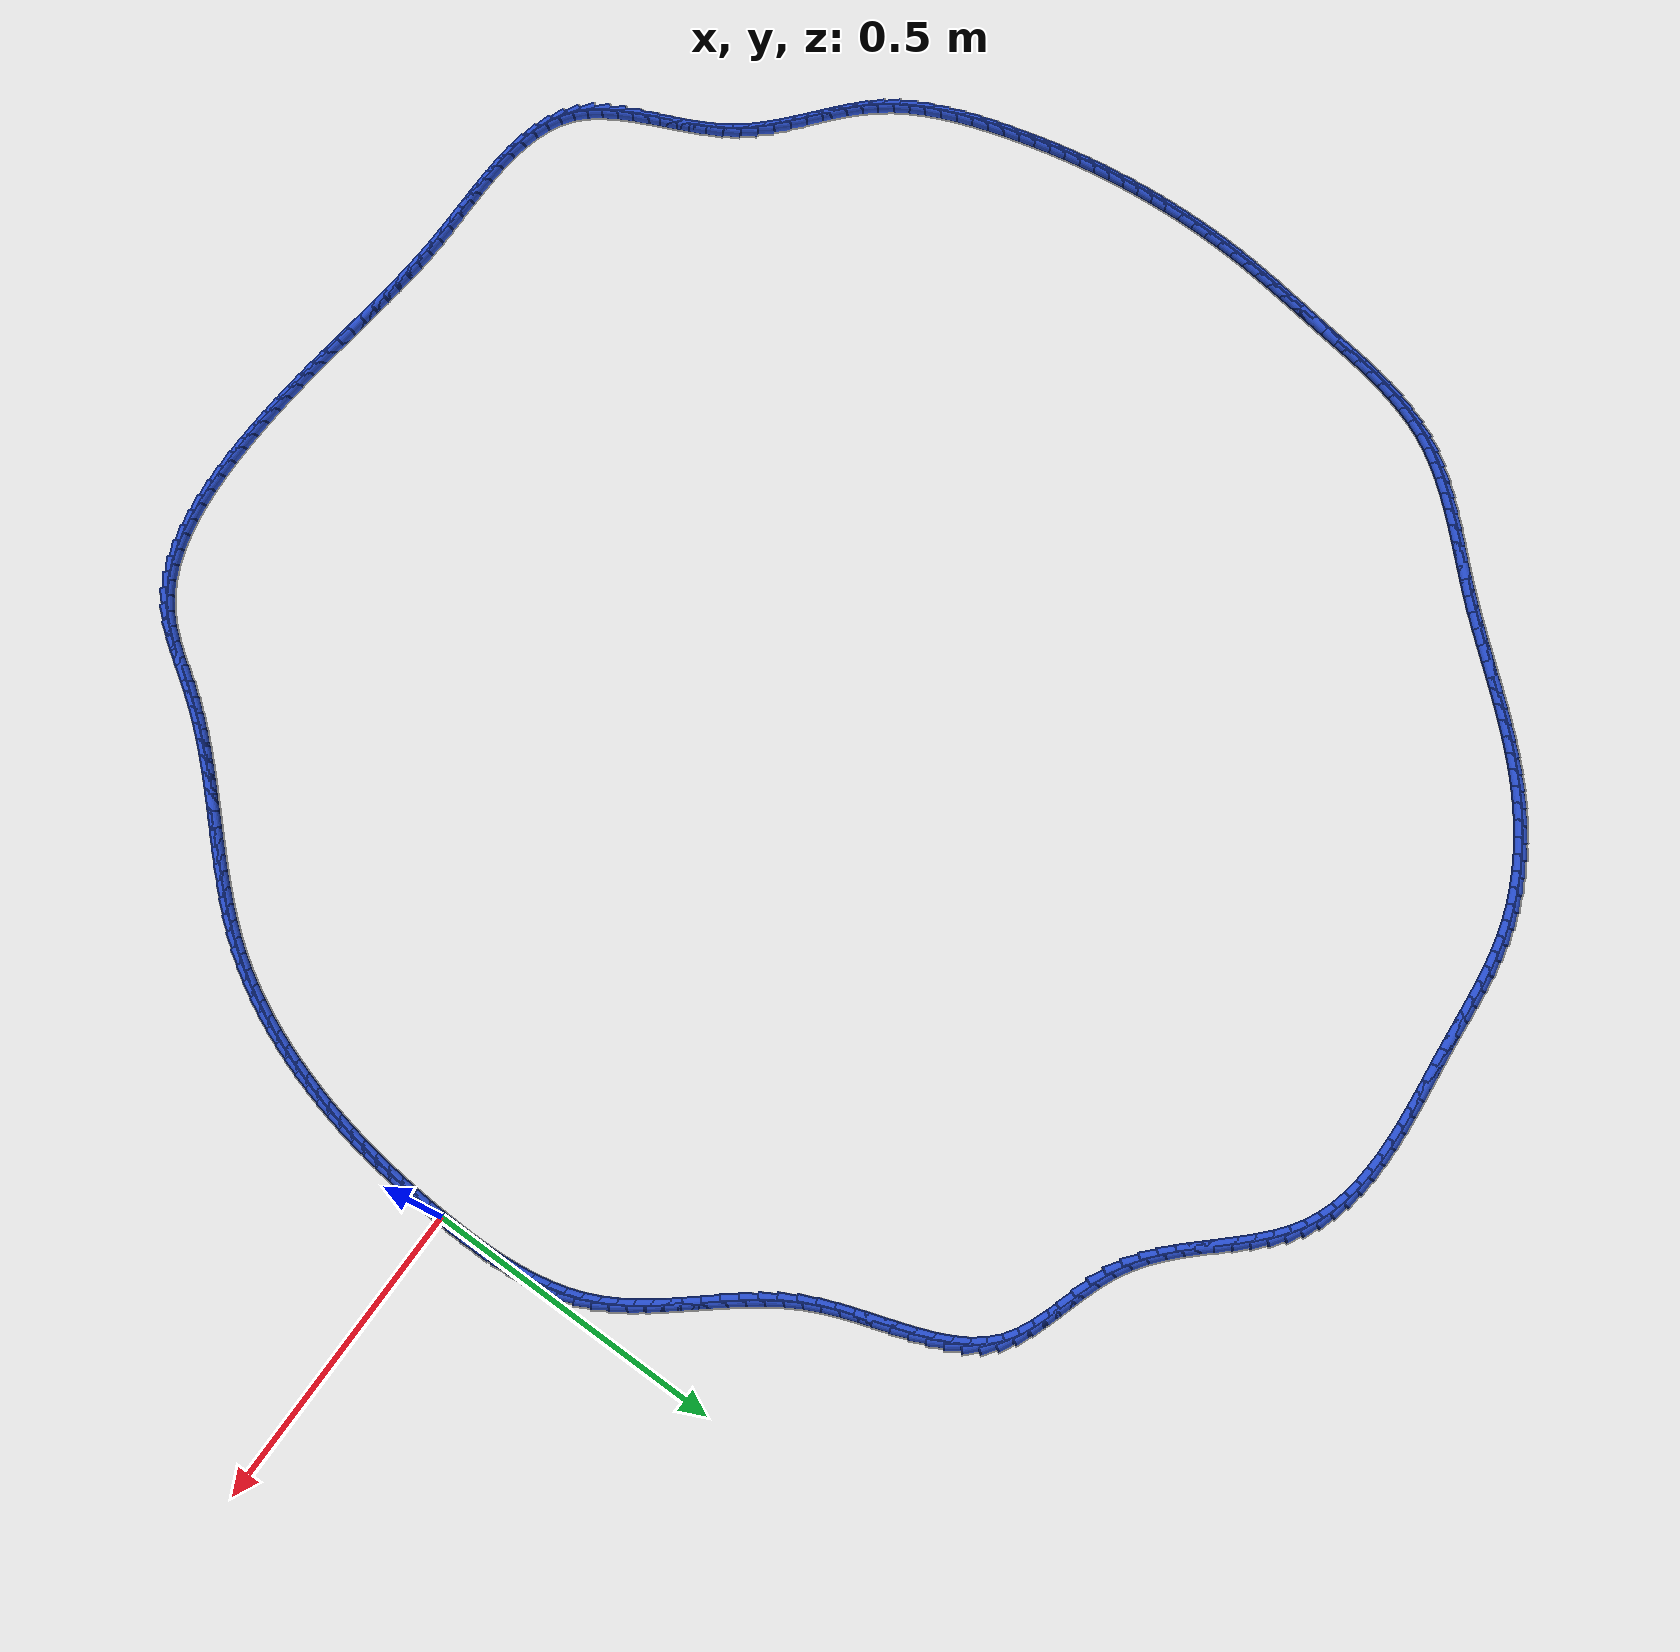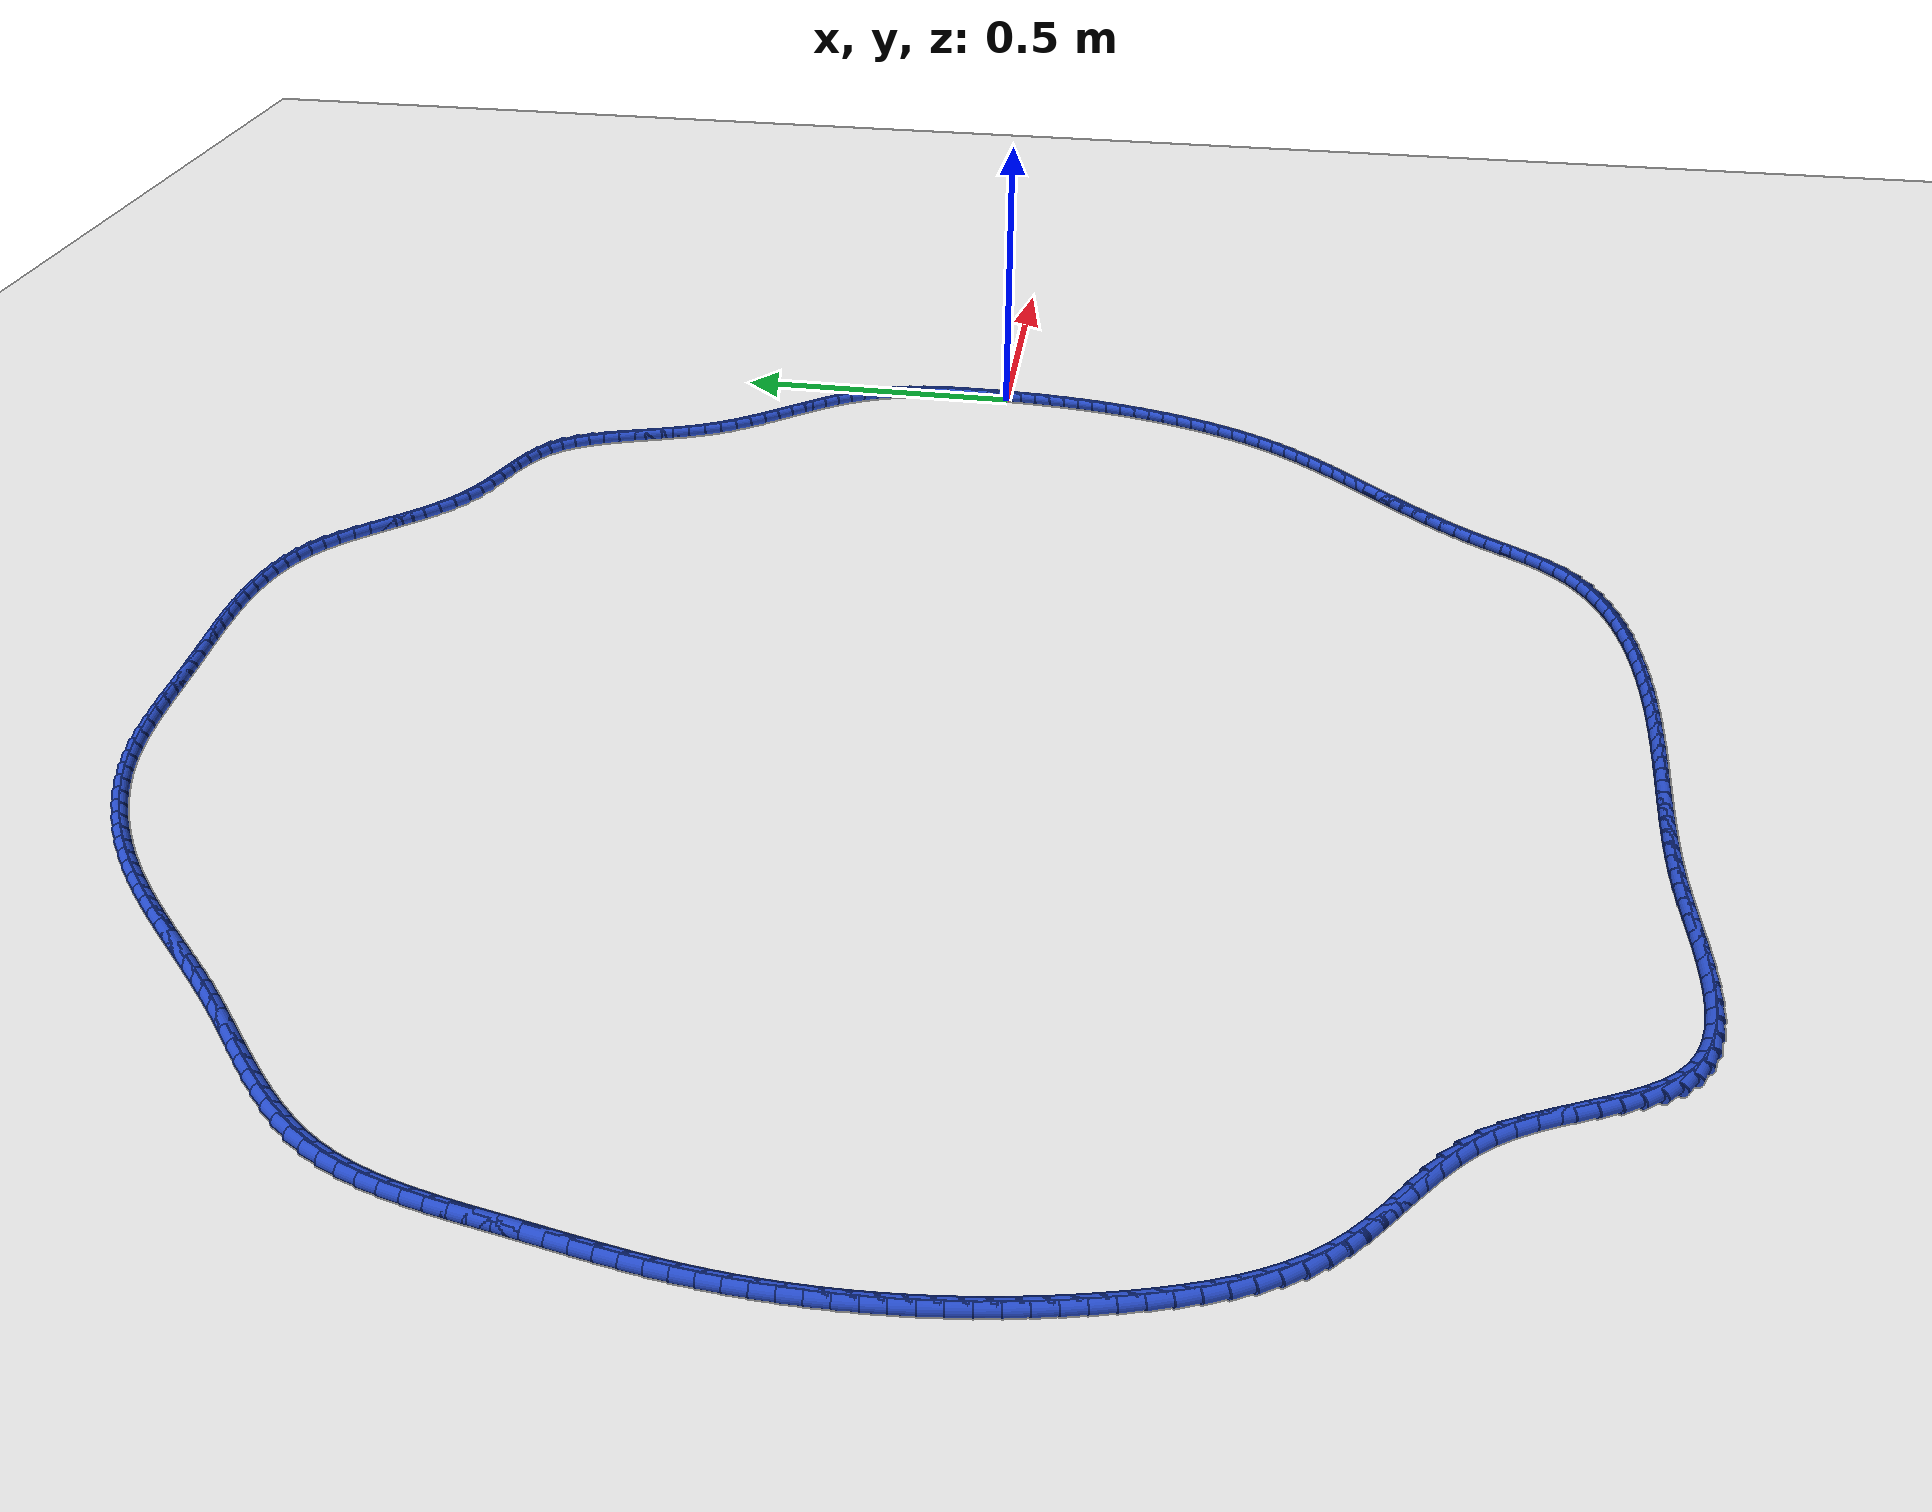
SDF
<sdf version="1.6">
 <world name="default">
  <light name="sun" type="directional">
   <pose>0 0 10 0 -0 0</pose>
   <diffuse>0.8 0.8 0.8 1</diffuse>
   <specular>0.2 0.2 0.2 1</specular>
   <attenuation>
    <range>1000</range>
    <constant>0.9</constant>
    <linear>0.01</linear>
    <quadratic>0.001</quadratic>
   </attenuation>
   <direction>-0.5 0.1 -0.9</direction>
  </light>
  <model name="ground_plane">
   <static>1</static>
   <link name="link">
    <collision name="collision">
     <geometry><plane><normal>0 0 1</normal><size>100 100</size></plane></geometry>
     <surface><friction><ode><mu>100</mu><mu2>50</mu2></ode></friction></surface>
    </collision>
    <visual name="visual">
     <cast_shadows>0</cast_shadows>
     <geometry><plane><normal>0 0 1</normal><size>100 100</size></plane></geometry>
     <material>
      <script><uri>file://media/materials/scripts/gazebo.material</uri><name>Gazebo/WhiteGlow</name></script>
     </material>
    </visual>
   </link>
  </model>
  <gravity>0 0 -9.8</gravity>
  <magnetic_field>6e-06 2.3e-05 -4.2e-05</magnetic_field>
  <atmosphere type="adiabatic"/>
  <physics name="default_physics" default="0" type="ode">
   <max_step_size>0.001</max_step_size>
   <real_time_factor>1</real_time_factor>
   <real_time_update_rate>1000</real_time_update_rate>
  </physics>
  <scene><ambient>0.4 0.4 0.4 1</ambient><background>0.7 0.7 0.7 1</background><shadows>1</shadows></scene>
  <spherical_coordinates>
   <surface_model>EARTH_WGS84</surface_model>
   <latitude_deg>0</latitude_deg>
   <longitude_deg>0</longitude_deg>
   <elevation>0</elevation>
   <heading_deg>0</heading_deg>
  </spherical_coordinates>
  <model name="line">
   <link name="link_0">
    <pose>-2.3744027577432547e-17 0.0 0.01 0 1.57 1.5411322489004222</pose>
    <collision name="collision">
     <geometry><cylinder><radius>0.01</radius><length>0.08</length></cylinder></geometry>
    </collision>
    <visual name="visual">
     <material>
      <script><name>Gazebo/Blue</name><uri>file://media/materials/scripts/gazebo.material</uri></script>
     </material>
     <geometry><cylinder><radius>0.01</radius><length>0.08</length></cylinder></geometry>
    </visual>
   </link>
   <link name="link_1">
    <pose>0.0008416605181511366 0.028364732303287784 0.01 0 1.57 1.5624884888304773</pose>
    <collision name="collision">
     <geometry><cylinder><radius>0.01</radius><length>0.08</length></cylinder></geometry>
    </collision>
    <visual name="visual">
     <material>
      <script><name>Gazebo/Blue</name><uri>file://media/materials/scripts/gazebo.material</uri></script>
     </material>
     <geometry><cylinder><radius>0.01</radius><length>0.08</length></cylinder></geometry>
    </visual>
   </link>
   <link name="link_2">
    <pose>0.0010783313936273008 0.056851738362290995 0.01 0 1.57 -1.5515653110899565</pose>
    <collision name="collision">
     <geometry><cylinder><radius>0.01</radius><length>0.08</length></cylinder></geometry>
    </collision>
    <visual name="visual">
     <material>
      <script><name>Gazebo/Blue</name><uri>file://media/materials/scripts/gazebo.material</uri></script>
     </material>
     <geometry><cylinder><radius>0.01</radius><length>0.08</length></cylinder></geometry>
    </visual>
   </link>
   <link name="link_3">
    <pose>0.0005308624911587484 0.08531624687828525 0.01 0 1.57 -1.517458055189469</pose>
    <collision name="collision">
     <geometry><cylinder><radius>0.01</radius><length>0.08</length></cylinder></geometry>
    </collision>
    <visual name="visual">
     <material>
      <script><name>Gazebo/Blue</name><uri>file://media/materials/scripts/gazebo.material</uri></script>
     </material>
     <geometry><cylinder><radius>0.01</radius><length>0.08</length></cylinder></geometry>
    </visual>
   </link>
   <link name="link_4">
    <pose>-0.0009798963245242348 0.11361348655254594 0.01 0 1.57 -1.476271643704682</pose>
    <collision name="collision">
     <geometry><cylinder><radius>0.01</radius><length>0.08</length></cylinder></geometry>
    </collision>
    <visual name="visual">
     <material>
      <script><name>Gazebo/Blue</name><uri>file://media/materials/scripts/gazebo.material</uri></script>
     </material>
     <geometry><cylinder><radius>0.01</radius><length>0.08</length></cylinder></geometry>
    </visual>
   </link>
   <link name="link_5">
    <pose>-0.0036330951886913657 0.14159868608634874 0.01 0 1.57 -1.4273986378362373</pose>
    <collision name="collision">
     <geometry><cylinder><radius>0.01</radius><length>0.08</length></cylinder></geometry>
    </collision>
    <visual name="visual">
     <material>
      <script><name>Gazebo/Blue</name><uri>file://media/materials/scripts/gazebo.material</uri></script>
     </material>
     <geometry><cylinder><radius>0.01</radius><length>0.08</length></cylinder></geometry>
    </visual>
   </link>
   <link name="link_6">
    <pose>-0.007607884236612364 0.16912707418096912 0.01 0 1.57 -1.370182999832</pose>
    <collision name="collision">
     <geometry><cylinder><radius>0.01</radius><length>0.08</length></cylinder></geometry>
    </collision>
    <visual name="visual">
     <material>
      <script><name>Gazebo/Blue</name><uri>file://media/materials/scripts/gazebo.material</uri></script>
     </material>
     <geometry><cylinder><radius>0.01</radius><length>0.08</length></cylinder></geometry>
    </visual>
   </link>
   <link name="link_7">
    <pose>-0.013083413603556944 0.19605387953768258 0.01 0 1.57 -1.3040005277934443</pose>
    <collision name="collision">
     <geometry><cylinder><radius>0.01</radius><length>0.08</length></cylinder></geometry>
    </collision>
    <visual name="visual">
     <material>
      <script><name>Gazebo/Blue</name><uri>file://media/materials/scripts/gazebo.material</uri></script>
     </material>
     <geometry><cylinder><radius>0.01</radius><length>0.08</length></cylinder></geometry>
    </visual>
   </link>
   <link name="link_8">
    <pose>-0.020238833424794822 0.22223433085776473 0.01 0 1.57 -1.2283841883100188</pose>
    <collision name="collision">
     <geometry><cylinder><radius>0.01</radius><length>0.08</length></cylinder></geometry>
    </collision>
    <visual name="visual">
     <material>
      <script><name>Gazebo/Blue</name><uri>file://media/materials/scripts/gazebo.material</uri></script>
     </material>
     <geometry><cylinder><radius>0.01</radius><length>0.08</length></cylinder></geometry>
    </visual>
   </link>
   <link name="link_9">
    <pose>-0.029253293835595714 0.2475236568424911 0.01 0 1.57 -1.1437988316661556</pose>
    <collision name="collision">
     <geometry><cylinder><radius>0.01</radius><length>0.08</length></cylinder></geometry>
    </collision>
    <visual name="visual">
     <material>
      <script><name>Gazebo/Blue</name><uri>file://media/materials/scripts/gazebo.material</uri></script>
     </material>
     <geometry><cylinder><radius>0.01</radius><length>0.08</length></cylinder></geometry>
    </visual>
   </link>
   <link name="link_10">
    <pose>-0.04029260205205641 0.2717863004527238 0.01 0 1.57 -1.062321657851553</pose>
    <collision name="collision">
     <geometry><cylinder><radius>0.01</radius><length>0.08</length></cylinder></geometry>
    </collision>
    <visual name="visual">
     <material>
      <script><name>Gazebo/Blue</name><uri>file://media/materials/scripts/gazebo.material</uri></script>
     </material>
     <geometry><cylinder><radius>0.01</radius><length>0.08</length></cylinder></geometry>
    </visual>
   </link>
   <link name="link_11">
    <pose>-0.053266393164274575 0.295063610200294 0.01 0 1.57 -0.9954584736030949</pose>
    <collision name="collision">
     <geometry><cylinder><radius>0.01</radius><length>0.08</length></cylinder></geometry>
    </collision>
    <visual name="visual">
     <material>
      <script><name>Gazebo/Blue</name><uri>file://media/materials/scripts/gazebo.material</uri></script>
     </material>
     <geometry><cylinder><radius>0.01</radius><length>0.08</length></cylinder></geometry>
    </visual>
   </link>
   <link name="link_12">
    <pose>-0.06785349010132992 0.31755632724116223 0.01 0 1.57 -0.9439994217995893</pose>
    <collision name="collision">
     <geometry><cylinder><radius>0.01</radius><length>0.08</length></cylinder></geometry>
    </collision>
    <visual name="visual">
     <material>
      <script><name>Gazebo/Blue</name><uri>file://media/materials/scripts/gazebo.material</uri></script>
     </material>
     <geometry><cylinder><radius>0.01</radius><length>0.08</length></cylinder></geometry>
    </visual>
   </link>
   <link name="link_13">
    <pose>-0.08372446215069532 0.33947089247325024 0.01 0 1.57 -0.9077357040851978</pose>
    <collision name="collision">
     <geometry><cylinder><radius>0.01</radius><length>0.08</length></cylinder></geometry>
    </collision>
    <visual name="visual">
     <material>
      <script><name>Gazebo/Blue</name><uri>file://media/materials/scripts/gazebo.material</uri></script>
     </material>
     <geometry><cylinder><radius>0.01</radius><length>0.08</length></cylinder></geometry>
    </visual>
   </link>
   <link name="link_14">
    <pose>-0.10054987859984388 0.3610137467944801 0.01 0 1.57 -0.8861976645155711</pose>
    <collision name="collision">
     <geometry><cylinder><radius>0.01</radius><length>0.08</length></cylinder></geometry>
    </collision>
    <visual name="visual">
     <material>
      <script><name>Gazebo/Blue</name><uri>file://media/materials/scripts/gazebo.material</uri></script>
     </material>
     <geometry><cylinder><radius>0.01</radius><length>0.08</length></cylinder></geometry>
    </visual>
   </link>
   <link name="link_15">
    <pose>-0.11800030873624849 0.3823913311027736 0.01 0 1.57 -0.8789013955237226</pose>
    <collision name="collision">
     <geometry><cylinder><radius>0.01</radius><length>0.08</length></cylinder></geometry>
    </collision>
    <visual name="visual">
     <material>
      <script><name>Gazebo/Blue</name><uri>file://media/materials/scripts/gazebo.material</uri></script>
     </material>
     <geometry><cylinder><radius>0.01</radius><length>0.08</length></cylinder></geometry>
    </visual>
   </link>
   <link name="link_16">
    <pose>-0.1357463218473822 0.4038100862960529 0.01 0 1.57 -0.885477847881823</pose>
    <collision name="collision">
     <geometry><cylinder><radius>0.01</radius><length>0.08</length></cylinder></geometry>
    </collision>
    <visual name="visual">
     <material>
      <script><name>Gazebo/Blue</name><uri>file://media/materials/scripts/gazebo.material</uri></script>
     </material>
     <geometry><cylinder><radius>0.01</radius><length>0.08</length></cylinder></geometry>
    </visual>
   </link>
   <link name="link_17">
    <pose>-0.153458487220718 0.4254764532722397 0.01 0 1.57 -0.9057065667550356</pose>
    <collision name="collision">
     <geometry><cylinder><radius>0.01</radius><length>0.08</length></cylinder></geometry>
    </collision>
    <visual name="visual">
     <material>
      <script><name>Gazebo/Blue</name><uri>file://media/materials/scripts/gazebo.material</uri></script>
     </material>
     <geometry><cylinder><radius>0.01</radius><length>0.08</length></cylinder></geometry>
    </visual>
   </link>
   <link name="link_18">
    <pose>-0.17080737414372885 0.447596872929256 0.01 0 1.57 -0.9394712555922621</pose>
    <collision name="collision">
     <geometry><cylinder><radius>0.01</radius><length>0.08</length></cylinder></geometry>
    </collision>
    <visual name="visual">
     <material>
      <script><name>Gazebo/Blue</name><uri>file://media/materials/scripts/gazebo.material</uri></script>
     </material>
     <geometry><cylinder><radius>0.01</radius><length>0.08</length></cylinder></geometry>
    </visual>
   </link>
   <link name="link_19">
    <pose>-0.18746355190388778 0.47037778616502385 0.01 0 1.57 -0.9866443600876831</pose>
    <collision name="collision">
     <geometry><cylinder><radius>0.01</radius><length>0.08</length></cylinder></geometry>
    </collision>
    <visual name="visual">
     <material>
      <script><name>Gazebo/Blue</name><uri>file://media/materials/scripts/gazebo.material</uri></script>
     </material>
     <geometry><cylinder><radius>0.01</radius><length>0.08</length></cylinder></geometry>
    </visual>
   </link>
   <link name="link_20">
    <pose>-0.2030975897886677 0.4940256338774649 0.01 0 1.57 -1.0469044571565393</pose>
    <collision name="collision">
     <geometry><cylinder><radius>0.01</radius><length>0.08</length></cylinder></geometry>
    </collision>
    <visual name="visual">
     <material>
      <script><name>Gazebo/Blue</name><uri>file://media/materials/scripts/gazebo.material</uri></script>
     </material>
     <geometry><cylinder><radius>0.01</radius><length>0.08</length></cylinder></geometry>
    </visual>
   </link>
   <link name="link_21">
    <pose>-0.2173800570855417 0.5187468569645014 0.01 0 1.57 -1.1184058844431575</pose>
    <collision name="collision">
     <geometry><cylinder><radius>0.01</radius><length>0.08</length></cylinder></geometry>
    </collision>
    <visual name="visual">
     <material>
      <script><name>Gazebo/Blue</name><uri>file://media/materials/scripts/gazebo.material</uri></script>
     </material>
     <geometry><cylinder><radius>0.01</radius><length>0.08</length></cylinder></geometry>
    </visual>
   </link>
   <link name="link_22">
    <pose>-0.23000680958957956 0.5447274703326499 0.01 0 1.57 -1.182380434496997</pose>
    <collision name="collision">
     <geometry><cylinder><radius>0.01</radius><length>0.08</length></cylinder></geometry>
    </collision>
    <visual name="visual">
     <material>
      <script><name>Gazebo/Blue</name><uri>file://media/materials/scripts/gazebo.material</uri></script>
     </material>
     <geometry><cylinder><radius>0.01</radius><length>0.08</length></cylinder></geometry>
    </visual>
   </link>
   <link name="link_23">
    <pose>-0.24109154040703054 0.5718159673349146 0.01 0 1.57 -1.225140455244971</pose>
    <collision name="collision">
     <geometry><cylinder><radius>0.01</radius><length>0.08</length></cylinder></geometry>
    </collision>
    <visual name="visual">
     <material>
      <script><name>Gazebo/Blue</name><uri>file://media/materials/scripts/gazebo.material</uri></script>
     </material>
     <geometry><cylinder><radius>0.01</radius><length>0.08</length></cylinder></geometry>
    </visual>
   </link>
   <link name="link_24">
    <pose>-0.25109106143106 0.5995836760666726 0.01 0 1.57 -1.2476132856732944</pose>
    <collision name="collision">
     <geometry><cylinder><radius>0.01</radius><length>0.08</length></cylinder></geometry>
    </collision>
    <visual name="visual">
     <material>
      <script><name>Gazebo/Blue</name><uri>file://media/materials/scripts/gazebo.material</uri></script>
     </material>
     <geometry><cylinder><radius>0.01</radius><length>0.08</length></cylinder></geometry>
    </visual>
   </link>
   <link name="link_25">
    <pose>-0.26047234529259766 0.6275937169599279 0.01 0 1.57 -1.250399248419881</pose>
    <collision name="collision">
     <geometry><cylinder><radius>0.01</radius><length>0.08</length></cylinder></geometry>
    </collision>
    <visual name="visual">
     <material>
      <script><name>Gazebo/Blue</name><uri>file://media/materials/scripts/gazebo.material</uri></script>
     </material>
     <geometry><cylinder><radius>0.01</radius><length>0.08</length></cylinder></geometry>
    </visual>
   </link>
   <link name="link_26">
    <pose>-0.2697023646225733 0.6554092104466842 0.01 0 1.57 -1.233095985175565</pose>
    <collision name="collision">
     <geometry><cylinder><radius>0.01</radius><length>0.08</length></cylinder></geometry>
    </collision>
    <visual name="visual">
     <material>
      <script><name>Gazebo/Blue</name><uri>file://media/materials/scripts/gazebo.material</uri></script>
     </material>
     <geometry><cylinder><radius>0.01</radius><length>0.08</length></cylinder></geometry>
    </visual>
   </link>
   <link name="link_27">
    <pose>-0.2792480920519167 0.6825932769589457 0.01 0 1.57 -1.1941876833717333</pose>
    <collision name="collision">
     <geometry><cylinder><radius>0.01</radius><length>0.08</length></cylinder></geometry>
    </collision>
    <visual name="visual">
     <material>
      <script><name>Gazebo/Blue</name><uri>file://media/materials/scripts/gazebo.material</uri></script>
     </material>
     <geometry><cylinder><radius>0.01</radius><length>0.08</length></cylinder></geometry>
    </visual>
   </link>
   <link name="link_28">
    <pose>-0.2895765002115575 0.7087090369287155 0.01 0 1.57 -1.1310663556052067</pose>
    <collision name="collision">
     <geometry><cylinder><radius>0.01</radius><length>0.08</length></cylinder></geometry>
    </collision>
    <visual name="visual">
     <material>
      <script><name>Gazebo/Blue</name><uri>file://media/materials/scripts/gazebo.material</uri></script>
     </material>
     <geometry><cylinder><radius>0.01</radius><length>0.08</length></cylinder></geometry>
    </visual>
   </link>
   <link name="link_29">
    <pose>-0.3011545617324257 0.7333196107879981 0.01 0 1.57 -1.0403753247503162</pose>
    <collision name="collision">
     <geometry><cylinder><radius>0.01</radius><length>0.08</length></cylinder></geometry>
    </collision>
    <visual name="visual">
     <material>
      <script><name>Gazebo/Blue</name><uri>file://media/materials/scripts/gazebo.material</uri></script>
     </material>
     <geometry><cylinder><radius>0.01</radius><length>0.08</length></cylinder></geometry>
    </visual>
   </link>
   <link name="link_30">
    <pose>-0.31444924924545065 0.7559881189687965 0.01 0 1.57 -0.9191095690090589</pose>
    <collision name="collision">
     <geometry><cylinder><radius>0.01</radius><length>0.08</length></cylinder></geometry>
    </collision>
    <visual name="visual">
     <material>
      <script><name>Gazebo/Blue</name><uri>file://media/materials/scripts/gazebo.material</uri></script>
     </material>
     <geometry><cylinder><radius>0.01</radius><length>0.08</length></cylinder></geometry>
    </visual>
   </link>
   <link name="link_31">
    <pose>-0.3299275353815625 0.7762776819031153 0.01 0 1.57 -0.766999354647303</pose>
    <collision name="collision">
     <geometry><cylinder><radius>0.01</radius><length>0.08</length></cylinder></geometry>
    </collision>
    <visual name="visual">
     <material>
      <script><name>Gazebo/Blue</name><uri>file://media/materials/scripts/gazebo.material</uri></script>
     </material>
     <geometry><cylinder><radius>0.01</radius><length>0.08</length></cylinder></geometry>
    </visual>
   </link>
   <link name="link_32">
    <pose>-0.34805639277169087 0.793751420022958 0.01 0 1.57 -0.5981969944369034</pose>
    <collision name="collision">
     <geometry><cylinder><radius>0.01</radius><length>0.08</length></cylinder></geometry>
    </collision>
    <visual name="visual">
     <material>
      <script><name>Gazebo/Blue</name><uri>file://media/materials/scripts/gazebo.material</uri></script>
     </material>
     <geometry><cylinder><radius>0.01</radius><length>0.08</length></cylinder></geometry>
    </visual>
   </link>
   <link name="link_33">
    <pose>-0.36915740236508815 0.808131614075938 0.01 0 1.57 -0.4644031500263688</pose>
    <collision name="collision">
     <geometry><cylinder><radius>0.01</radius><length>0.08</length></cylinder></geometry>
    </collision>
    <visual name="visual">
     <material>
      <script><name>Gazebo/Blue</name><uri>file://media/materials/scripts/gazebo.material</uri></script>
     </material>
     <geometry><cylinder><radius>0.01</radius><length>0.08</length></cylinder></geometry>
    </visual>
   </link>
   <link name="link_34">
    <pose>-0.39279289832779907 0.8199716924808923 0.01 0 1.57 -0.37812577525415075</pose>
    <collision name="collision">
     <geometry><cylinder><radius>0.01</radius><length>0.08</length></cylinder></geometry>
    </collision>
    <visual name="visual">
     <material>
      <script><name>Gazebo/Blue</name><uri>file://media/materials/scripts/gazebo.material</uri></script>
     </material>
     <geometry><cylinder><radius>0.01</radius><length>0.08</length></cylinder></geometry>
    </visual>
   </link>
   <link name="link_35">
    <pose>-0.4182781922926956 0.8300954992945325 0.01 0 1.57 -0.3334597781663252</pose>
    <collision name="collision">
     <geometry><cylinder><radius>0.01</radius><length>0.08</length></cylinder></geometry>
    </collision>
    <visual name="visual">
     <material>
      <script><name>Gazebo/Blue</name><uri>file://media/materials/scripts/gazebo.material</uri></script>
     </material>
     <geometry><cylinder><radius>0.01</radius><length>0.08</length></cylinder></geometry>
    </visual>
   </link>
   <link name="link_36">
    <pose>-0.44492846297600935 0.8393270240774552 0.01 0 1.57 -0.3257179871921345</pose>
    <collision name="collision">
     <geometry><cylinder><radius>0.01</radius><length>0.08</length></cylinder></geometry>
    </collision>
    <visual name="visual">
     <material>
      <script><name>Gazebo/Blue</name><uri>file://media/materials/scripts/gazebo.material</uri></script>
     </material>
     <geometry><cylinder><radius>0.01</radius><length>0.08</length></cylinder></geometry>
    </visual>
   </link>
   <link name="link_37">
    <pose>-0.4720588890939725 0.8484902563902554 0.01 0 1.57 -0.3529548242485485</pose>
    <collision name="collision">
     <geometry><cylinder><radius>0.01</radius><length>0.08</length></cylinder></geometry>
    </collision>
    <visual name="visual">
     <material>
      <script><name>Gazebo/Blue</name><uri>file://media/materials/scripts/gazebo.material</uri></script>
     </material>
     <geometry><cylinder><radius>0.01</radius><length>0.08</length></cylinder></geometry>
    </visual>
   </link>
   <link name="link_38">
    <pose>-0.49898464936281695 0.8584091857935302 0.01 0 1.57 -0.4158786364964564</pose>
    <collision name="collision">
     <geometry><cylinder><radius>0.01</radius><length>0.08</length></cylinder></geometry>
    </collision>
    <visual name="visual">
     <material>
      <script><name>Gazebo/Blue</name><uri>file://media/materials/scripts/gazebo.material</uri></script>
     </material>
     <geometry><cylinder><radius>0.01</radius><length>0.08</length></cylinder></geometry>
    </visual>
   </link>
   <link name="link_39">
    <pose>-0.5250209224987745 0.8699078018478746 0.01 0 1.57 -0.5147075791965274</pose>
    <collision name="collision">
     <geometry><cylinder><radius>0.01</radius><length>0.08</length></cylinder></geometry>
    </collision>
    <visual name="visual">
     <material>
      <script><name>Gazebo/Blue</name><uri>file://media/materials/scripts/gazebo.material</uri></script>
     </material>
     <geometry><cylinder><radius>0.01</radius><length>0.08</length></cylinder></geometry>
    </visual>
   </link>
   <link name="link_40">
    <pose>-0.5495181094205166 0.8837623225067062 0.01 0 1.57 -0.6187239867300558</pose>
    <collision name="collision">
     <geometry><cylinder><radius>0.01</radius><length>0.08</length></cylinder></geometry>
    </collision>
    <visual name="visual">
     <material>
      <script><name>Gazebo/Blue</name><uri>file://media/materials/scripts/gazebo.material</uri></script>
     </material>
     <geometry><cylinder><radius>0.01</radius><length>0.08</length></cylinder></geometry>
    </visual>
   </link>
   <link name="link_41">
    <pose>-0.5723600686253677 0.9000254412380728 0.01 0 1.57 -0.701814720372819</pose>
    <collision name="collision">
     <geometry><cylinder><radius>0.01</radius><length>0.08</length></cylinder></geometry>
    </collision>
    <visual name="visual">
     <material>
      <script><name>Gazebo/Blue</name><uri>file://media/materials/scripts/gazebo.material</uri></script>
     </material>
     <geometry><cylinder><radius>0.01</radius><length>0.08</length></cylinder></geometry>
    </visual>
   </link>
   <link name="link_42">
    <pose>-0.5938446284844653 0.9181883872963794 0.01 0 1.57 -0.7629746549043068</pose>
    <collision name="collision">
     <geometry><cylinder><radius>0.01</radius><length>0.08</length></cylinder></geometry>
    </collision>
    <visual name="visual">
     <material>
      <script><name>Gazebo/Blue</name><uri>file://media/materials/scripts/gazebo.material</uri></script>
     </material>
     <geometry><cylinder><radius>0.01</radius><length>0.08</length></cylinder></geometry>
    </visual>
   </link>
   <link name="link_43">
    <pose>-0.6142804592573747 0.9377276851646332 0.01 0 1.57 -0.8027682768963464</pose>
    <collision name="collision">
     <geometry><cylinder><radius>0.01</radius><length>0.08</length></cylinder></geometry>
    </collision>
    <visual name="visual">
     <material>
      <script><name>Gazebo/Blue</name><uri>file://media/materials/scripts/gazebo.material</uri></script>
     </material>
     <geometry><cylinder><radius>0.01</radius><length>0.08</length></cylinder></geometry>
    </visual>
   </link>
   <link name="link_44">
    <pose>-0.6339762312036605 0.9581198593258405 0.01 0 1.57 -0.8218246254023871</pose>
    <collision name="collision">
     <geometry><cylinder><radius>0.01</radius><length>0.08</length></cylinder></geometry>
    </collision>
    <visual name="visual">
     <material>
      <script><name>Gazebo/Blue</name><uri>file://media/materials/scripts/gazebo.material</uri></script>
     </material>
     <geometry><cylinder><radius>0.01</radius><length>0.08</length></cylinder></geometry>
    </visual>
   </link>
   <link name="link_45">
    <pose>-0.6532406145828885 0.9788414342630085 0.01 0 1.57 -0.8203187812267426</pose>
    <collision name="collision">
     <geometry><cylinder><radius>0.01</radius><length>0.08</length></cylinder></geometry>
    </collision>
    <visual name="visual">
     <material>
      <script><name>Gazebo/Blue</name><uri>file://media/materials/scripts/gazebo.material</uri></script>
     </material>
     <geometry><cylinder><radius>0.01</radius><length>0.08</length></cylinder></geometry>
    </visual>
   </link>
   <link name="link_46">
    <pose>-0.6723822796546233 0.9993689344591437 0.01 0 1.57 -0.7977215788457497</pose>
    <collision name="collision">
     <geometry><cylinder><radius>0.01</radius><length>0.08</length></cylinder></geometry>
    </collision>
    <visual name="visual">
     <material>
      <script><name>Gazebo/Blue</name><uri>file://media/materials/scripts/gazebo.material</uri></script>
     </material>
     <geometry><cylinder><radius>0.01</radius><length>0.08</length></cylinder></geometry>
    </visual>
   </link>
   <link name="link_47">
    <pose>-0.69170989667843 1.0191788843972531 0.01 0 1.57 -0.7527638277051322</pose>
    <collision name="collision">
     <geometry><cylinder><radius>0.01</radius><length>0.08</length></cylinder></geometry>
    </collision>
    <visual name="visual">
     <material>
      <script><name>Gazebo/Blue</name><uri>file://media/materials/scripts/gazebo.material</uri></script>
     </material>
     <geometry><cylinder><radius>0.01</radius><length>0.08</length></cylinder></geometry>
    </visual>
   </link>
   <link name="link_48">
    <pose>-0.7115321359138738 1.0377478085603429 0.01 0 1.57 -0.6836636817662294</pose>
    <collision name="collision">
     <geometry><cylinder><radius>0.01</radius><length>0.08</length></cylinder></geometry>
    </collision>
    <visual name="visual">
     <material>
      <script><name>Gazebo/Blue</name><uri>file://media/materials/scripts/gazebo.material</uri></script>
     </material>
     <geometry><cylinder><radius>0.01</radius><length>0.08</length></cylinder></geometry>
    </visual>
   </link>
   <link name="link_49">
    <pose>-0.73215766762052 1.0545522314314209 0.01 0 1.57 -0.5887919030432144</pose>
    <collision name="collision">
     <geometry><cylinder><radius>0.01</radius><length>0.08</length></cylinder></geometry>
    </collision>
    <visual name="visual">
     <material>
      <script><name>Gazebo/Blue</name><uri>file://media/materials/scripts/gazebo.material</uri></script>
     </material>
     <geometry><cylinder><radius>0.01</radius><length>0.08</length></cylinder></geometry>
    </visual>
   </link>
   <link name="link_50">
    <pose>-0.7538951566658616 1.0690686867431753 0.01 0 1.57 -0.47445630878375933</pose>
    <collision name="collision">
     <geometry><cylinder><radius>0.01</radius><length>0.08</length></cylinder></geometry>
    </collision>
    <visual name="visual">
     <material>
      <script><name>Gazebo/Blue</name><uri>file://media/materials/scripts/gazebo.material</uri></script>
     </material>
     <geometry><cylinder><radius>0.01</radius><length>0.08</length></cylinder></geometry>
    </visual>
   </link>
   <link name="link_51">
    <pose>-0.7769686414914742 1.0809188783145813 0.01 0 1.57 -0.3656989024934782</pose>
    <collision name="collision">
     <geometry><cylinder><radius>0.01</radius><length>0.08</length></cylinder></geometry>
    </collision>
    <visual name="visual">
     <material>
      <script><name>Gazebo/Blue</name><uri>file://media/materials/scripts/gazebo.material</uri></script>
     </material>
     <geometry><cylinder><radius>0.01</radius><length>0.08</length></cylinder></geometry>
    </visual>
   </link>
   <link name="link_52">
    <pose>-0.8013032989616099 1.090237183878206 0.01 0 1.57 -0.2695992211025664</pose>
    <collision name="collision">
     <geometry><cylinder><radius>0.01</radius><length>0.08</length></cylinder></geometry>
    </collision>
    <visual name="visual">
     <material>
      <script><name>Gazebo/Blue</name><uri>file://media/materials/scripts/gazebo.material</uri></script>
     </material>
     <geometry><cylinder><radius>0.01</radius><length>0.08</length></cylinder></geometry>
    </visual>
   </link>
   <link name="link_53">
    <pose>-0.8267583646446277 1.0972710983579699 0.01 0 1.57 -0.1868279581467998</pose>
    <collision name="collision">
     <geometry><cylinder><radius>0.01</radius><length>0.08</length></cylinder></geometry>
    </collision>
    <visual name="visual">
     <material>
      <script><name>Gazebo/Blue</name><uri>file://media/materials/scripts/gazebo.material</uri></script>
     </material>
     <geometry><cylinder><radius>0.01</radius><length>0.08</length></cylinder></geometry>
    </visual>
   </link>
   <link name="link_54">
    <pose>-0.8531930741088881 1.102268116677797 0.01 0 1.57 -0.11707111752358872</pose>
    <collision name="collision">
     <geometry><cylinder><radius>0.01</radius><length>0.08</length></cylinder></geometry>
    </collision>
    <visual name="visual">
     <material>
      <script><name>Gazebo/Blue</name><uri>file://media/materials/scripts/gazebo.material</uri></script>
     </material>
     <geometry><cylinder><radius>0.01</radius><length>0.08</length></cylinder></geometry>
    </visual>
   </link>
   <link name="link_55">
    <pose>-0.8804666629227509 1.1054757337616095 0.01 0 1.57 -0.05947960817188597</pose>
    <collision name="collision">
     <geometry><cylinder><radius>0.01</radius><length>0.08</length></cylinder></geometry>
    </collision>
    <visual name="visual">
     <material>
      <script><name>Gazebo/Blue</name><uri>file://media/materials/scripts/gazebo.material</uri></script>
     </material>
     <geometry><cylinder><radius>0.01</radius><length>0.08</length></cylinder></geometry>
    </visual>
   </link>
   <link name="link_56">
    <pose>-0.9084383666545763 1.1071414445333292 0.01 0 1.57 -0.013014045916830596</pose>
    <collision name="collision">
     <geometry><cylinder><radius>0.01</radius><length>0.08</length></cylinder></geometry>
    </collision>
    <visual name="visual">
     <material>
      <script><name>Gazebo/Blue</name><uri>file://media/materials/scripts/gazebo.material</uri></script>
     </material>
     <geometry><cylinder><radius>0.01</radius><length>0.08</length></cylinder></geometry>
    </visual>
   </link>
   <link name="link_57">
    <pose>-0.9369674208727242 1.1075127439168797 0.01 0 1.57 0.023336655295008665</pose>
    <collision name="collision">
     <geometry><cylinder><radius>0.01</radius><length>0.08</length></cylinder></geometry>
    </collision>
    <visual name="visual">
     <material>
      <script><name>Gazebo/Blue</name><uri>file://media/materials/scripts/gazebo.material</uri></script>
     </material>
     <geometry><cylinder><radius>0.01</radius><length>0.08</length></cylinder></geometry>
    </visual>
   </link>
   <link name="link_58">
    <pose>-0.965913061145555 1.1068371268361825 0.01 0 1.57 0.05043511267824467</pose>
    <collision name="collision">
     <geometry><cylinder><radius>0.01</radius><length>0.08</length></cylinder></geometry>
    </collision>
    <visual name="visual">
     <material>
      <script><name>Gazebo/Blue</name><uri>file://media/materials/scripts/gazebo.material</uri></script>
     </material>
     <geometry><cylinder><radius>0.01</radius><length>0.08</length></cylinder></geometry>
    </visual>
   </link>
   <link name="link_59">
    <pose>-0.9951345230414284 1.1053620882151611 0.01 0 1.57 0.06893709986470267</pose>
    <collision name="collision">
     <geometry><cylinder><radius>0.01</radius><length>0.08</length></cylinder></geometry>
    </collision>
    <visual name="visual">
     <material>
      <script><name>Gazebo/Blue</name><uri>file://media/materials/scripts/gazebo.material</uri></script>
     </material>
     <geometry><cylinder><radius>0.01</radius><length>0.08</length></cylinder></geometry>
    </visual>
   </link>
   <link name="link_60">
    <pose>-1.0244910421287046 1.1033351229777373 0.01 0 1.57 0.07926568217834067</pose>
    <collision name="collision">
     <geometry><cylinder><radius>0.01</radius><length>0.08</length></cylinder></geometry>
    </collision>
    <visual name="visual">
     <material>
      <script><name>Gazebo/Blue</name><uri>file://media/materials/scripts/gazebo.material</uri></script>
     </material>
     <geometry><cylinder><radius>0.01</radius><length>0.08</length></cylinder></geometry>
    </visual>
   </link>
   <link name="link_61">
    <pose>-1.053841853975743 1.1010037260478336 0.01 0 1.57 0.08159850793330946</pose>
    <collision name="collision">
     <geometry><cylinder><radius>0.01</radius><length>0.08</length></cylinder></geometry>
    </collision>
    <visual name="visual">
     <material>
      <script><name>Gazebo/Blue</name><uri>file://media/materials/scripts/gazebo.material</uri></script>
     </material>
     <geometry><cylinder><radius>0.01</radius><length>0.08</length></cylinder></geometry>
    </visual>
   </link>
   <link name="link_62">
    <pose>-1.0830461941509046 1.0986153923493729 0.01 0 1.57 0.07588325117777958</pose>
    <collision name="collision">
     <geometry><cylinder><radius>0.01</radius><length>0.08</length></cylinder></geometry>
    </collision>
    <visual name="visual">
     <material>
      <script><name>Gazebo/Blue</name><uri>file://media/materials/scripts/gazebo.material</uri></script>
     </material>
     <geometry><cylinder><radius>0.01</radius><length>0.08</length></cylinder></geometry>
    </visual>
   </link>
   <link name="link_63">
    <pose>-1.1119635499738292 1.0964168277786615 0.01 0 1.57 0.06673845027058287</pose>
    <collision name="collision">
     <geometry><cylinder><radius>0.01</radius><length>0.08</length></cylinder></geometry>
    </collision>
    <visual name="visual">
     <material>
      <script><name>Gazebo/Blue</name><uri>file://media/materials/scripts/gazebo.material</uri></script>
     </material>
     <geometry><cylinder><radius>0.01</radius><length>0.08</length></cylinder></geometry>
    </visual>
   </link>
   <link name="link_64">
    <pose>-1.140499738308713 1.094509534243048 0.01 0 1.57 0.06483117132982656</pose>
    <collision name="collision">
     <geometry><cylinder><radius>0.01</radius><length>0.08</length></cylinder></geometry>
    </collision>
    <visual name="visual">
     <material>
      <script><name>Gazebo/Blue</name><uri>file://media/materials/scripts/gazebo.material</uri></script>
     </material>
     <geometry><cylinder><radius>0.01</radius><length>0.08</length></cylinder></geometry>
    </visual>
   </link>
   <link name="link_65">
    <pose>-1.1686606822779055 1.0926812650874371 0.01 0 1.57 0.0718926721216693</pose>
    <collision name="collision">
     <geometry><cylinder><radius>0.01</radius><length>0.08</length></cylinder></geometry>
    </collision>
    <visual name="visual">
     <material>
      <script><name>Gazebo/Blue</name><uri>file://media/materials/scripts/gazebo.material</uri></script>
     </material>
     <geometry><cylinder><radius>0.01</radius><length>0.08</length></cylinder></geometry>
    </visual>
   </link>
   <link name="link_66">
    <pose>-1.1964653586273453 1.0906788615727943 0.01 0 1.57 0.08822787158191177</pose>
    <collision name="collision">
     <geometry><cylinder><radius>0.01</radius><length>0.08</length></cylinder></geometry>
    </collision>
    <visual name="visual">
     <material>
      <script><name>Gazebo/Blue</name><uri>file://media/materials/scripts/gazebo.material</uri></script>
     </material>
     <geometry><cylinder><radius>0.01</radius><length>0.08</length></cylinder></geometry>
    </visual>
   </link>
   <link name="link_67">
    <pose>-1.2239327441029715 1.0882491649600858 0.01 0 1.57 0.11406096073007319</pose>
    <collision name="collision">
     <geometry><cylinder><radius>0.01</radius><length>0.08</length></cylinder></geometry>
    </collision>
    <visual name="visual">
     <material>
      <script><name>Gazebo/Blue</name><uri>file://media/materials/scripts/gazebo.material</uri></script>
     </material>
     <geometry><cylinder><radius>0.01</radius><length>0.08</length></cylinder></geometry>
    </visual>
   </link>
   <link name="link_68">
    <pose>-1.251081815450724 1.0851390165102783 0.01 0 1.57 0.14948357932419815</pose>
    <collision name="collision">
     <geometry><cylinder><radius>0.01</radius><length>0.08</length></cylinder></geometry>
    </collision>
    <visual name="visual">
     <material>
      <script><name>Gazebo/Blue</name><uri>file://media/materials/scripts/gazebo.material</uri></script>
     </material>
     <geometry><cylinder><radius>0.01</radius><length>0.08</length></cylinder></geometry>
    </visual>
   </link>
   <link name="link_69">
    <pose>-1.2779315494165413 1.081095257484337 0.01 0 1.57 0.19437746728670596</pose>
    <collision name="collision">
     <geometry><cylinder><radius>0.01</radius><length>0.08</length></cylinder></geometry>
    </collision>
    <visual name="visual">
     <material>
      <script><name>Gazebo/Blue</name><uri>file://media/materials/scripts/gazebo.material</uri></script>
     </material>
     <geometry><cylinder><radius>0.01</radius><length>0.08</length></cylinder></geometry>
    </visual>
   </link>
   <link name="link_70">
    <pose>-1.3045009227463635 1.0758647291432293 0.01 0 1.57 0.2483193841789385</pose>
    <collision name="collision">
     <geometry><cylinder><radius>0.01</radius><length>0.08</length></cylinder></geometry>
    </collision>
    <visual name="visual">
     <material>
      <script><name>Gazebo/Blue</name><uri>file://media/materials/scripts/gazebo.material</uri></script>
     </material>
     <geometry><cylinder><radius>0.01</radius><length>0.08</length></cylinder></geometry>
    </visual>
   </link>
   <link name="link_71">
    <pose>-1.3308089121861293 1.0691942727479211 0.01 0 1.57 0.3087406517517289</pose>
    <collision name="collision">
     <geometry><cylinder><radius>0.01</radius><length>0.08</length></cylinder></geometry>
    </collision>
    <visual name="visual">
     <material>
      <script><name>Gazebo/Blue</name><uri>file://media/materials/scripts/gazebo.material</uri></script>
     </material>
     <geometry><cylinder><radius>0.01</radius><length>0.08</length></cylinder></geometry>
    </visual>
   </link>
   <link name="link_72">
    <pose>-1.3568584716286476 1.060886039423066 0.01 0 1.57 0.3672539704113925</pose>
    <collision name="collision">
     <geometry><cylinder><radius>0.01</radius><length>0.08</length></cylinder></geometry>
    </collision>
    <visual name="visual">
     <material>
      <script><name>Gazebo/Blue</name><uri>file://media/materials/scripts/gazebo.material</uri></script>
     </material>
     <geometry><cylinder><radius>0.01</radius><length>0.08</length></cylinder></geometry>
    </visual>
   </link>
   <link name="link_73">
    <pose>-1.38258060566893 1.0509905446652081 0.01 0 1.57 0.42203436986433046</pose>
    <collision name="collision">
     <geometry><cylinder><radius>0.01</radius><length>0.08</length></cylinder></geometry>
    </collision>
    <visual name="visual">
     <material>
      <script><name>Gazebo/Blue</name><uri>file://media/materials/scripts/gazebo.material</uri></script>
     </material>
     <geometry><cylinder><radius>0.01</radius><length>0.08</length></cylinder></geometry>
    </visual>
   </link>
   <link name="link_74">
    <pose>-1.4078861320751148 1.0396279876054928 0.01 0 1.57 0.4735832295844764</pose>
    <collision name="collision">
     <geometry><cylinder><radius>0.01</radius><length>0.08</length></cylinder></geometry>
    </collision>
    <visual name="visual">
     <material>
      <script><name>Gazebo/Blue</name><uri>file://media/materials/scripts/gazebo.material</uri></script>
     </material>
     <geometry><cylinder><radius>0.01</radius><length>0.08</length></cylinder></geometry>
    </visual>
   </link>
   <link name="link_75">
    <pose>-1.4326858675852274 1.0269185709309387 0.01 0 1.57 0.5224033971049021</pose>
    <collision name="collision">
     <geometry><cylinder><radius>0.01</radius><length>0.08</length></cylinder></geometry>
    </collision>
    <visual name="visual">
     <material>
      <script><name>Gazebo/Blue</name><uri>file://media/materials/scripts/gazebo.material</uri></script>
     </material>
     <geometry><cylinder><radius>0.01</radius><length>0.08</length></cylinder></geometry>
    </visual>
   </link>
   <link name="link_76">
    <pose>-1.4568906289372938 1.0129824973285653 0.01 0 1.57 0.5689916413756373</pose>
    <collision name="collision">
     <geometry><cylinder><radius>0.01</radius><length>0.08</length></cylinder></geometry>
    </collision>
    <visual name="visual">
     <material>
      <script><name>Gazebo/Blue</name><uri>file://media/materials/scripts/gazebo.material</uri></script>
     </material>
     <geometry><cylinder><radius>0.01</radius><length>0.08</length></cylinder></geometry>
    </visual>
   </link>
   <link name="link_77">
    <pose>-1.4804112328693413 0.9979399694853917 0.01 0 1.57 0.6138376171303522</pose>
    <collision name="collision">
     <geometry><cylinder><radius>0.01</radius><length>0.08</length></cylinder></geometry>
    </collision>
    <visual name="visual">
     <material>
      <script><name>Gazebo/Blue</name><uri>file://media/materials/scripts/gazebo.material</uri></script>
     </material>
     <geometry><cylinder><radius>0.01</radius><length>0.08</length></cylinder></geometry>
    </visual>
   </link>
   <link name="link_78">
    <pose>-1.503158496119396 0.9819111900884373 0.01 0 1.57 0.6571451216572342</pose>
    <collision name="collision">
     <geometry><cylinder><radius>0.01</radius><length>0.08</length></cylinder></geometry>
    </collision>
    <visual name="visual">
     <material>
      <script><name>Gazebo/Blue</name><uri>file://media/materials/scripts/gazebo.material</uri></script>
     </material>
     <geometry><cylinder><radius>0.01</radius><length>0.08</length></cylinder></geometry>
    </visual>
   </link>
   <link name="link_79">
    <pose>-1.5250587650274183 0.9650142449809376 0.01 0 1.57 0.6968904264008976</pose>
    <collision name="collision">
     <geometry><cylinder><radius>0.01</radius><length>0.08</length></cylinder></geometry>
    </collision>
    <visual name="visual">
     <material>
      <script><name>Gazebo/Blue</name><uri>file://media/materials/scripts/gazebo.material</uri></script>
     </material>
     <geometry><cylinder><radius>0.01</radius><length>0.08</length></cylinder></geometry>
    </visual>
   </link>
   <link name="link_80">
    <pose>-1.5461630706263914 0.9473502242055551 0.01 0 1.57 0.7317518147637724</pose>
    <collision name="collision">
     <geometry><cylinder><radius>0.01</radius><length>0.08</length></cylinder></geometry>
    </collision>
    <visual name="visual">
     <material>
      <script><name>Gazebo/Blue</name><uri>file://media/materials/scripts/gazebo.material</uri></script>
     </material>
     <geometry><cylinder><radius>0.01</radius><length>0.08</length></cylinder></geometry>
    </visual>
   </link>
   <link name="link_81">
    <pose>-1.566582456503655 0.929012037479199 0.01 0 1.57 0.7615051513535609</pose>
    <collision name="collision">
     <geometry><cylinder><radius>0.01</radius><length>0.08</length></cylinder></geometry>
    </collision>
    <visual name="visual">
     <material>
      <script><name>Gazebo/Blue</name><uri>file://media/materials/scripts/gazebo.material</uri></script>
     </material>
     <geometry><cylinder><radius>0.01</radius><length>0.08</length></cylinder></geometry>
    </visual>
   </link>
   <link name="link_82">
    <pose>-1.5864283499607457 0.9100925422146036 0.01 0 1.57 0.7860198943883514</pose>
    <collision name="collision">
     <geometry><cylinder><radius>0.01</radius><length>0.08</length></cylinder></geometry>
    </collision>
    <visual name="visual">
     <material>
      <script><name>Gazebo/Blue</name><uri>file://media/materials/scripts/gazebo.material</uri></script>
     </material>
     <geometry><cylinder><radius>0.01</radius><length>0.08</length></cylinder></geometry>
    </visual>
   </link>
   <link name="link_83">
    <pose>-1.6058121782991996 0.8906845958245011 0.01 0 1.57 0.805231155553182</pose>
    <collision name="collision">
     <geometry><cylinder><radius>0.01</radius><length>0.08</length></cylinder></geometry>
    </collision>
    <visual name="visual">
     <material>
      <script><name>Gazebo/Blue</name><uri>file://media/materials/scripts/gazebo.material</uri></script>
     </material>
     <geometry><cylinder><radius>0.01</radius><length>0.08</length></cylinder></geometry>
    </visual>
   </link>
   <link name="link_84">
    <pose>-1.6248453688205537 0.8708810557216262 0.01 0 1.57 0.8191202783906381</pose>
    <collision name="collision">
     <geometry><cylinder><radius>0.01</radius><length>0.08</length></cylinder></geometry>
    </collision>
    <visual name="visual">
     <material>
      <script><name>Gazebo/Blue</name><uri>file://media/materials/scripts/gazebo.material</uri></script>
     </material>
     <geometry><cylinder><radius>0.01</radius><length>0.08</length></cylinder></geometry>
    </visual>
   </link>
   <link name="link_85">
    <pose>-1.6436393488263463 0.8507747793187116 0.01 0 1.57 0.8276986964187525</pose>
    <collision name="collision">
     <geometry><cylinder><radius>0.01</radius><length>0.08</length></cylinder></geometry>
    </collision>
    <visual name="visual">
     <material>
      <script><name>Gazebo/Blue</name><uri>file://media/materials/scripts/gazebo.material</uri></script>
     </material>
     <geometry><cylinder><radius>0.01</radius><length>0.08</length></cylinder></geometry>
    </visual>
   </link>
   <link name="link_86">
    <pose>-1.6623055456181122 0.8304586240284919 0.01 0 1.57 0.8309959671210732</pose>
    <collision name="collision">
     <geometry><cylinder><radius>0.01</radius><length>0.08</length></cylinder></geometry>
    </collision>
    <visual name="visual">
     <material>
      <script><name>Gazebo/Blue</name><uri>file://media/materials/scripts/gazebo.material</uri></script>
     </material>
     <geometry><cylinder><radius>0.01</radius><length>0.08</length></cylinder></geometry>
    </visual>
   </link>
   <link name="link_87">
    <pose>-1.6809553864973892 0.8100254472637002 0.01 0 1.57 0.8290523032095672</pose>
    <collision name="collision">
     <geometry><cylinder><radius>0.01</radius><length>0.08</length></cylinder></geometry>
    </collision>
    <visual name="visual">
     <material>
      <script><name>Gazebo/Blue</name><uri>file://media/materials/scripts/gazebo.material</uri></script>
     </material>
     <geometry><cylinder><radius>0.01</radius><length>0.08</length></cylinder></geometry>
    </visual>
   </link>
   <link name="link_88">
    <pose>-1.6997002987657146 0.7895681064370703 0.01 0 1.57 0.8219155874910257</pose>
    <collision name="collision">
     <geometry><cylinder><radius>0.01</radius><length>0.08</length></cylinder></geometry>
    </collision>
    <visual name="visual">
     <material>
      <script><name>Gazebo/Blue</name><uri>file://media/materials/scripts/gazebo.material</uri></script>
     </material>
     <geometry><cylinder><radius>0.01</radius><length>0.08</length></cylinder></geometry>
    </visual>
   </link>
   <link name="link_89">
    <pose>-1.718651709724625 0.7691794589613357 0.01 0 1.57 0.8096426839496936</pose>
    <collision name="collision">
     <geometry><cylinder><radius>0.01</radius><length>0.08</length></cylinder></geometry>
    </collision>
    <visual name="visual">
     <material>
      <script><name>Gazebo/Blue</name><uri>file://media/materials/scripts/gazebo.material</uri></script>
     </material>
     <geometry><cylinder><radius>0.01</radius><length>0.08</length></cylinder></geometry>
    </visual>
   </link>
   <link name="link_90">
    <pose>-1.7379210466756567 0.7489523622492301 0.01 0 1.57 0.7923131474276485</pose>
    <collision name="collision">
     <geometry><cylinder><radius>0.01</radius><length>0.08</length></cylinder></geometry>
    </collision>
    <visual name="visual">
     <material>
      <script><name>Gazebo/Blue</name><uri>file://media/materials/scripts/gazebo.material</uri></script>
     </material>
     <geometry><cylinder><radius>0.01</radius><length>0.08</length></cylinder></geometry>
    </visual>
   </link>
   <link name="link_91">
    <pose>-1.7576195366123262 0.7289795414598592 0.01 0 1.57 0.7737002986561314</pose>
    <collision name="collision">
     <geometry><cylinder><radius>0.01</radius><length>0.08</length></cylinder></geometry>
    </collision>
    <visual name="visual">
     <material>
      <script><name>Gazebo/Blue</name><uri>file://media/materials/scripts/gazebo.material</uri></script>
     </material>
     <geometry><cylinder><radius>0.01</radius><length>0.08</length></cylinder></geometry>
    </visual>
   </link>
   <link name="link_92">
    <pose>-1.7777698360719294 0.7092952429948615 0.01 0 1.57 0.7632057205534214</pose>
    <collision name="collision">
     <geometry><cylinder><radius>0.01</radius><length>0.08</length></cylinder></geometry>
    </collision>
    <visual name="visual">
     <material>
      <script><name>Gazebo/Blue</name><uri>file://media/materials/scripts/gazebo.material</uri></script>
     </material>
     <geometry><cylinder><radius>0.01</radius><length>0.08</length></cylinder></geometry>
    </visual>
   </link>
   <link name="link_93">
    <pose>-1.798167280129087 0.689783623968202 0.01 0 1.57 0.7621982476762261</pose>
    <collision name="collision">
     <geometry><cylinder><radius>0.01</radius><length>0.08</length></cylinder></geometry>
    </collision>
    <visual name="visual">
     <material>
      <script><name>Gazebo/Blue</name><uri>file://media/materials/scripts/gazebo.material</uri></script>
     </material>
     <geometry><cylinder><radius>0.01</radius><length>0.08</length></cylinder></geometry>
    </visual>
   </link>
   <link name="link_94">
    <pose>-1.8185712425278597 0.670305097979162 0.01 0 1.57 0.7706881947209409</pose>
    <collision name="collision">
     <geometry><cylinder><radius>0.01</radius><length>0.08</length></cylinder></geometry>
    </collision>
    <visual name="visual">
     <material>
      <script><name>Gazebo/Blue</name><uri>file://media/materials/scripts/gazebo.material</uri></script>
     </material>
     <geometry><cylinder><radius>0.01</radius><length>0.08</length></cylinder></geometry>
    </visual>
   </link>
   <link name="link_95">
    <pose>-1.8387410970123113 0.6507200786270221 0.01 0 1.57 0.7888383675781363</pose>
    <collision name="collision">
     <geometry><cylinder><radius>0.01</radius><length>0.08</length></cylinder></geometry>
    </collision>
    <visual name="visual">
     <material>
      <script><name>Gazebo/Blue</name><uri>file://media/materials/scripts/gazebo.material</uri></script>
     </material>
     <geometry><cylinder><radius>0.01</radius><length>0.08</length></cylinder></geometry>
    </visual>
   </link>
   <link name="link_96">
    <pose>-1.858436217326503 0.6308889795110629 0.01 0 1.57 0.8169467498425644</pose>
    <collision name="collision">
     <geometry><cylinder><radius>0.01</radius><length>0.08</length></cylinder></geometry>
    </collision>
    <visual name="visual">
     <material>
      <script><name>Gazebo/Blue</name><uri>file://media/materials/scripts/gazebo.material</uri></script>
     </material>
     <geometry><cylinder><radius>0.01</radius><length>0.08</length></cylinder></geometry>
    </visual>
   </link>
   <link name="link_97">
    <pose>-1.877415977214497 0.6106722142305656 0.01 0 1.57 0.8554032547266549</pose>
    <collision name="collision">
     <geometry><cylinder><radius>0.01</radius><length>0.08</length></cylinder></geometry>
    </collision>
    <visual name="visual">
     <material>
      <script><name>Gazebo/Blue</name><uri>file://media/materials/scripts/gazebo.material</uri></script>
     </material>
     <geometry><cylinder><radius>0.01</radius><length>0.08</length></cylinder></geometry>
    </visual>
   </link>
   <link name="link_98">
    <pose>-1.8954397504203562 0.5899301963848109 0.01 0 1.57 0.9046108766442557</pose>
    <collision name="collision">
     <geometry><cylinder><radius>0.01</radius><length>0.08</length></cylinder></geometry>
    </collision>
    <visual name="visual">
     <material>
      <script><name>Gazebo/Blue</name><uri>file://media/materials/scripts/gazebo.material</uri></script>
     </material>
     <geometry><cylinder><radius>0.01</radius><length>0.08</length></cylinder></geometry>
    </visual>
   </link>
   <link name="link_99">
    <pose>-1.9122669106881418 0.5685233395730793 0.01 0 1.57 0.9648597801944171</pose>
    <collision name="collision">
     <geometry><cylinder><radius>0.01</radius><length>0.08</length></cylinder></geometry>
    </collision>
    <visual name="visual">
     <material>
      <script><name>Gazebo/Blue</name><uri>file://media/materials/scripts/gazebo.material</uri></script>
     </material>
     <geometry><cylinder><radius>0.01</radius><length>0.08</length></cylinder></geometry>
    </visual>
   </link>
   <link name="link_100">
    <pose>-1.9276568317619174 0.5463120573946518 0.01 0 1.57 1.0361481505127497</pose>
    <collision name="collision">
     <geometry><cylinder><radius>0.01</radius><length>0.08</length></cylinder></geometry>
    </collision>
    <visual name="visual">
     <material>
      <script><name>Gazebo/Blue</name><uri>file://media/materials/scripts/gazebo.material</uri></script>
     </material>
     <geometry><cylinder><radius>0.01</radius><length>0.08</length></cylinder></geometry>
    </visual>
   </link>
   <link name="link_101">
    <pose>-1.9413688873857438 0.5231567634488093 0.01 0 1.57 1.114810387325386</pose>
    <collision name="collision">
     <geometry><cylinder><radius>0.01</radius><length>0.08</length></cylinder></geometry>
    </collision>
    <visual name="visual">
     <material>
      <script><name>Gazebo/Blue</name><uri>file://media/materials/scripts/gazebo.material</uri></script>
     </material>
     <geometry><cylinder><radius>0.01</radius><length>0.08</length></cylinder></geometry>
    </visual>
   </link>
   <link name="link_102">
    <pose>-1.9532353547929067 0.49896216054540987 0.01 0 1.57 1.1866396649966138</pose>
    <collision name="collision">
     <geometry><cylinder><radius>0.01</radius><length>0.08</length></cylinder></geometry>
    </collision>
    <visual name="visual">
     <material>
      <script><name>Gazebo/Blue</name><uri>file://media/materials/scripts/gazebo.material</uri></script>
     </material>
     <geometry><cylinder><radius>0.01</radius><length>0.08</length></cylinder></geometry>
    </visual>
   </link>
   <link name="link_103">
    <pose>-1.963398356713197 0.4738211840821822 0.01 0 1.57 1.2478036752640835</pose>
    <collision name="collision">
     <geometry><cylinder><radius>0.01</radius><length>0.08</length></cylinder></geometry>
    </collision>
    <visual name="visual">
     <material>
      <script><name>Gazebo/Blue</name><uri>file://media/materials/scripts/gazebo.material</uri></script>
     </material>
     <geometry><cylinder><radius>0.01</radius><length>0.08</length></cylinder></geometry>
    </visual>
   </link>
   <link name="link_104">
    <pose>-1.9720823165234624 0.4478767674847543 0.01 0 1.57 1.2984861281508806</pose>
    <collision name="collision">
     <geometry><cylinder><radius>0.01</radius><length>0.08</length></cylinder></geometry>
    </collision>
    <visual name="visual">
     <material>
      <script><name>Gazebo/Blue</name><uri>file://media/materials/scripts/gazebo.material</uri></script>
     </material>
     <geometry><cylinder><radius>0.01</radius><length>0.08</length></cylinder></geometry>
    </visual>
   </link>
   <link name="link_105">
    <pose>-1.9795116582403096 0.42127184456741174 0.01 0 1.57 1.3390984253755343</pose>
    <collision name="collision">
     <geometry><cylinder><radius>0.01</radius><length>0.08</length></cylinder></geometry>
    </collision>
    <visual name="visual">
     <material>
      <script><name>Gazebo/Blue</name><uri>file://media/materials/scripts/gazebo.material</uri></script>
     </material>
     <geometry><cylinder><radius>0.01</radius><length>0.08</length></cylinder></geometry>
    </visual>
   </link>
   <link name="link_106">
    <pose>-1.985910805880345 0.39414934914443855 0.01 0 1.57 1.37011760212782</pose>
    <collision name="collision">
     <geometry><cylinder><radius>0.01</radius><length>0.08</length></cylinder></geometry>
    </collision>
    <visual name="visual">
     <material>
      <script><name>Gazebo/Blue</name><uri>file://media/materials/scripts/gazebo.material</uri></script>
     </material>
     <geometry><cylinder><radius>0.01</radius><length>0.08</length></cylinder></geometry>
    </visual>
   </link>
   <link name="link_107">
    <pose>-1.9915041834601732 0.3666522150301193 0.01 0 1.57 1.3919754883610613</pose>
    <collision name="collision">
     <geometry><cylinder><radius>0.01</radius><length>0.08</length></cylinder></geometry>
    </collision>
    <visual name="visual">
     <material>
      <script><name>Gazebo/Blue</name><uri>file://media/materials/scripts/gazebo.material</uri></script>
     </material>
     <geometry><cylinder><radius>0.01</radius><length>0.08</length></cylinder></geometry>
    </visual>
   </link>
   <link name="link_108">
    <pose>-1.996516214996402 0.3389233760387384 0.01 0 1.57 1.4049887167758068</pose>
    <collision name="collision">
     <geometry><cylinder><radius>0.01</radius><length>0.08</length></cylinder></geometry>
    </collision>
    <visual name="visual">
     <material>
      <script><name>Gazebo/Blue</name><uri>file://media/materials/scripts/gazebo.material</uri></script>
     </material>
     <geometry><cylinder><radius>0.01</radius><length>0.08</length></cylinder></geometry>
    </visual>
   </link>
   <link name="link_109">
    <pose>-2.001171324505637 0.31110576598458106 0.01 0 1.57 1.4093166347816044</pose>
    <collision name="collision">
     <geometry><cylinder><radius>0.01</radius><length>0.08</length></cylinder></geometry>
    </collision>
    <visual name="visual">
     <material>
      <script><name>Gazebo/Blue</name><uri>file://media/materials/scripts/gazebo.material</uri></script>
     </material>
     <geometry><cylinder><radius>0.01</radius><length>0.08</length></cylinder></geometry>
    </visual>
   </link>
   <link name="link_110">
    <pose>-2.0056939360044836 0.2833423186819314 0.01 0 1.57 1.4064392846585951</pose>
    <collision name="collision">
     <geometry><cylinder><radius>0.01</radius><length>0.08</length></cylinder></geometry>
    </collision>
    <visual name="visual">
     <material>
      <script><name>Gazebo/Blue</name><uri>file://media/materials/scripts/gazebo.material</uri></script>
     </material>
     <geometry><cylinder><radius>0.01</radius><length>0.08</length></cylinder></geometry>
    </visual>
   </link>
   <link name="link_111">
    <pose>-2.0102694812862465 0.25575438732183786 0.01 0 1.57 1.4048451146574836</pose>
    <collision name="collision">
     <geometry><cylinder><radius>0.01</radius><length>0.08</length></cylinder></geometry>
    </collision>
    <visual name="visual">
     <material>
      <script><name>Gazebo/Blue</name><uri>file://media/materials/scripts/gazebo.material</uri></script>
     </material>
     <geometry><cylinder><radius>0.01</radius><length>0.08</length></cylinder></geometry>
    </visual>
   </link>
   <link name="link_112">
    <pose>-2.014861110557623 0.22834030120066914 0.01 0 1.57 1.4076223490007251</pose>
    <collision name="collision">
     <geometry><cylinder><radius>0.01</radius><length>0.08</length></cylinder></geometry>
    </collision>
    <visual name="visual">
     <material>
      <script><name>Gazebo/Blue</name><uri>file://media/materials/scripts/gazebo.material</uri></script>
     </material>
     <geometry><cylinder><radius>0.01</radius><length>0.08</length></cylinder></geometry>
    </visual>
   </link>
   <link name="link_113">
    <pose>-2.0193533249227245 0.20105486050804078 0.01 0 1.57 1.4148347682911617</pose>
    <collision name="collision">
     <geometry><cylinder><radius>0.01</radius><length>0.08</length></cylinder></geometry>
    </collision>
    <visual name="visual">
     <material>
      <script><name>Gazebo/Blue</name><uri>file://media/materials/scripts/gazebo.material</uri></script>
     </material>
     <geometry><cylinder><radius>0.01</radius><length>0.08</length></cylinder></geometry>
    </visual>
   </link>
   <link name="link_114">
    <pose>-2.023630534329399 0.17385281498224908 0.01 0 1.57 1.4265169240975755</pose>
    <collision name="collision">
     <geometry><cylinder><radius>0.01</radius><length>0.08</length></cylinder></geometry>
    </collision>
    <visual name="visual">
     <material>
      <script><name>Gazebo/Blue</name><uri>file://media/materials/scripts/gazebo.material</uri></script>
     </material>
     <geometry><cylinder><radius>0.01</radius><length>0.08</length></cylinder></geometry>
    </visual>
   </link>
   <link name="link_115">
    <pose>-2.0275771487254937 0.14668891436159032 0.01 0 1.57 1.4426724614749207</pose>
    <collision name="collision">
     <geometry><cylinder><radius>0.01</radius><length>0.08</length></cylinder></geometry>
    </collision>
    <visual name="visual">
     <material>
      <script><name>Gazebo/Blue</name><uri>file://media/materials/scripts/gazebo.material</uri></script>
     </material>
     <geometry><cylinder><radius>0.01</radius><length>0.08</length></cylinder></geometry>
    </visual>
   </link>
   <link name="link_116">
    <pose>-2.0310775780588526 0.11951790838436188 0.01 0 1.57 1.4632358579321882</pose>
    <collision name="collision">
     <geometry><cylinder><radius>0.01</radius><length>0.08</length></cylinder></geometry>
    </collision>
    <visual name="visual">
     <material>
      <script><name>Gazebo/Blue</name><uri>file://media/materials/scripts/gazebo.material</uri></script>
     </material>
     <geometry><cylinder><radius>0.01</radius><length>0.08</length></cylinder></geometry>
    </visual>
   </link>
   <link name="link_117">
    <pose>-2.0340170401562734 0.09229491855707603 0.01 0 1.57 1.4864393853423197</pose>
    <collision name="collision">
     <geometry><cylinder><radius>0.01</radius><length>0.08</length></cylinder></geometry>
    </collision>
    <visual name="visual">
     <material>
      <script><name>Gazebo/Blue</name><uri>file://media/materials/scripts/gazebo.material</uri></script>
     </material>
     <geometry><cylinder><radius>0.01</radius><length>0.08</length></cylinder></geometry>
    </visual>
   </link>
   <link name="link_118">
    <pose>-2.036325404109787 0.06499561392150699 0.01 0 1.57 1.5097000524742115</pose>
    <collision name="collision">
     <geometry><cylinder><radius>0.01</radius><length>0.08</length></cylinder></geometry>
    </collision>
    <visual name="visual">
     <material>
      <script><name>Gazebo/Blue</name><uri>file://media/materials/scripts/gazebo.material</uri></script>
     </material>
     <geometry><cylinder><radius>0.01</radius><length>0.08</length></cylinder></geometry>
    </visual>
   </link>
   <link name="link_119">
    <pose>-2.037999636230829 0.03762654019166562 0.01 0 1.57 1.5328048510033225</pose>
    <collision name="collision">
     <geometry><cylinder><radius>0.01</radius><length>0.08</length></cylinder></geometry>
    </collision>
    <visual name="visual">
     <material>
      <script><name>Gazebo/Blue</name><uri>file://media/materials/scripts/gazebo.material</uri></script>
     </material>
     <geometry><cylinder><radius>0.01</radius><length>0.08</length></cylinder></geometry>
    </visual>
   </link>
   <link name="link_120">
    <pose>-2.0390422346312964 0.010196788695096699 0.01 0 1.57 1.555752241240177</pose>
    <collision name="collision">
     <geometry><cylinder><radius>0.01</radius><length>0.08</length></cylinder></geometry>
    </collision>
    <visual name="visual">
     <material>
      <script><name>Gazebo/Blue</name><uri>file://media/materials/scripts/gazebo.material</uri></script>
     </material>
     <geometry><cylinder><radius>0.01</radius><length>0.08</length></cylinder></geometry>
    </visual>
   </link>
   <link name="link_121">
    <pose>-2.0394556974230853 -0.017284549240656186 0.01 0 1.57 -1.5630513865373092</pose>
    <collision name="collision">
     <geometry><cylinder><radius>0.01</radius><length>0.08</length></cylinder></geometry>
    </collision>
    <visual name="visual">
     <material>
      <script><name>Gazebo/Blue</name><uri>file://media/materials/scripts/gazebo.material</uri></script>
     </material>
     <geometry><cylinder><radius>0.01</radius><length>0.08</length></cylinder></geometry>
    </visual>
   </link>
   <link name="link_122">
    <pose>-2.039242522718092 -0.04480838228804897 0.01 0 1.57 -1.5404211276250255</pose>
    <collision name="collision">
     <geometry><cylinder><radius>0.01</radius><length>0.08</length></cylinder></geometry>
    </collision>
    <visual name="visual">
     <material>
      <script><name>Gazebo/Blue</name><uri>file://media/materials/scripts/gazebo.material</uri></script>
     </material>
     <geometry><cylinder><radius>0.01</radius><length>0.08</length></cylinder></geometry>
    </visual>
   </link>
   <link name="link_123">
    <pose>-2.0384052086282143 -0.07236561911953765 0.01 0 1.57 -1.5179495156313365</pose>
    <collision name="collision">
     <geometry><cylinder><radius>0.01</radius><length>0.08</length></cylinder></geometry>
    </collision>
    <visual name="visual">
     <material>
      <script><name>Gazebo/Blue</name><uri>file://media/materials/scripts/gazebo.material</uri></script>
     </material>
     <geometry><cylinder><radius>0.01</radius><length>0.08</length></cylinder></geometry>
    </visual>
   </link>
   <link name="link_124">
    <pose>-2.036946253265346 -0.09994716840757818 0.01 0 1.57 -1.4956359402491022</pose>
    <collision name="collision">
     <geometry><cylinder><radius>0.01</radius><length>0.08</length></cylinder></geometry>
    </collision>
    <visual name="visual">
     <material>
      <script><name>Gazebo/Blue</name><uri>file://media/materials/scripts/gazebo.material</uri></script>
     </material>
     <geometry><cylinder><radius>0.01</radius><length>0.08</length></cylinder></geometry>
    </visual>
   </link>
   <link name="link_125">
    <pose>-2.0348681547413863 -0.12754393882462736 0.01 0 1.57 -1.4734793335671696</pose>
    <collision name="collision">
     <geometry><cylinder><radius>0.01</radius><length>0.08</length></cylinder></geometry>
    </collision>
    <visual name="visual">
     <material>
      <script><name>Gazebo/Blue</name><uri>file://media/materials/scripts/gazebo.material</uri></script>
     </material>
     <geometry><cylinder><radius>0.01</radius><length>0.08</length></cylinder></geometry>
    </visual>
   </link>
   <link name="link_126">
    <pose>-2.032173411168231 -0.1551468390431396 0.01 0 1.57 -1.4514782030770943</pose>
    <collision name="collision">
     <geometry><cylinder><radius>0.01</radius><length>0.08</length></cylinder></geometry>
    </collision>
    <visual name="visual">
     <material>
      <script><name>Gazebo/Blue</name><uri>file://media/materials/scripts/gazebo.material</uri></script>
     </material>
     <geometry><cylinder><radius>0.01</radius><length>0.08</length></cylinder></geometry>
    </visual>
   </link>
   <link name="link_127">
    <pose>-2.028864520657775 -0.18274677773557174 0.01 0 1.57 -1.4296306646881176</pose>
    <collision name="collision">
     <geometry><cylinder><radius>0.01</radius><length>0.08</length></cylinder></geometry>
    </collision>
    <visual name="visual">
     <material>
      <script><name>Gazebo/Blue</name><uri>file://media/materials/scripts/gazebo.material</uri></script>
     </material>
     <geometry><cylinder><radius>0.01</radius><length>0.08</length></cylinder></geometry>
    </visual>
   </link>
   <link name="link_128">
    <pose>-2.024943981321917 -0.2103346635743796 0.01 0 1.57 -1.407934475508109</pose>
    <collision name="collision">
     <geometry><cylinder><radius>0.01</radius><length>0.08</length></cylinder></geometry>
    </collision>
    <visual name="visual">
     <material>
      <script><name>Gazebo/Blue</name><uri>file://media/materials/scripts/gazebo.material</uri></script>
     </material>
     <geometry><cylinder><radius>0.01</radius><length>0.08</length></cylinder></geometry>
    </visual>
   </link>
   <link name="link_129">
    <pose>-2.020414291272553 -0.2379014052320193 0.01 0 1.57 -1.3863870661801525</pose>
    <collision name="collision">
     <geometry><cylinder><radius>0.01</radius><length>0.08</length></cylinder></geometry>
    </collision>
    <visual name="visual">
     <material>
      <script><name>Gazebo/Blue</name><uri>file://media/materials/scripts/gazebo.material</uri></script>
     </material>
     <geometry><cylinder><radius>0.01</radius><length>0.08</length></cylinder></geometry>
    </visual>
   </link>
   <link name="link_130">
    <pose>-2.015277948621579 -0.2654379113809468 0.01 0 1.57 -1.3649855725942714</pose>
    <collision name="collision">
     <geometry><cylinder><radius>0.01</radius><length>0.08</length></cylinder></geometry>
    </collision>
    <visual name="visual">
     <material>
      <script><name>Gazebo/Blue</name><uri>file://media/materials/scripts/gazebo.material</uri></script>
     </material>
     <geometry><cylinder><radius>0.01</radius><length>0.08</length></cylinder></geometry>
    </visual>
   </link>
   <link name="link_131">
    <pose>-2.0095374514808912 -0.292935090693618 0.01 0 1.57 -1.3437268668236417</pose>
    <collision name="collision">
     <geometry><cylinder><radius>0.01</radius><length>0.08</length></cylinder></geometry>
    </collision>
    <visual name="visual">
     <material>
      <script><name>Gazebo/Blue</name><uri>file://media/materials/scripts/gazebo.material</uri></script>
     </material>
     <geometry><cylinder><radius>0.01</radius><length>0.08</length></cylinder></geometry>
    </visual>
   </link>
   <link name="link_132">
    <pose>-2.0031952979623866 -0.32038385184248974 0.01 0 1.57 -1.3226075871620044</pose>
    <collision name="collision">
     <geometry><cylinder><radius>0.01</radius><length>0.08</length></cylinder></geometry>
    </collision>
    <visual name="visual">
     <material>
      <script><name>Gazebo/Blue</name><uri>file://media/materials/scripts/gazebo.material</uri></script>
     </material>
     <geometry><cylinder><radius>0.01</radius><length>0.08</length></cylinder></geometry>
    </visual>
   </link>
   <link name="link_133">
    <pose>-1.9962539861779622 -0.3477751035000165 0.01 0 1.57 -1.301099924794298</pose>
    <collision name="collision">
     <geometry><cylinder><radius>0.01</radius><length>0.08</length></cylinder></geometry>
    </collision>
    <visual name="visual">
     <material>
      <script><name>Gazebo/Blue</name><uri>file://media/materials/scripts/gazebo.material</uri></script>
     </material>
     <geometry><cylinder><radius>0.01</radius><length>0.08</length></cylinder></geometry>
    </visual>
   </link>
   <link name="link_134">
    <pose>-1.9887041230786748 -0.37508699905204107 0.01 0 1.57 -1.2745186344548505</pose>
    <collision name="collision">
     <geometry><cylinder><radius>0.01</radius><length>0.08</length></cylinder></geometry>
    </collision>
    <visual name="visual">
     <material>
      <script><name>Gazebo/Blue</name><uri>file://media/materials/scripts/gazebo.material</uri></script>
     </material>
     <geometry><cylinder><radius>0.01</radius><length>0.08</length></cylinder></geometry>
    </visual>
   </link>
   <link name="link_135">
    <pose>-1.980431908513148 -0.40218569756070355 0.01 0 1.57 -1.2401494269079516</pose>
    <collision name="collision">
     <geometry><cylinder><radius>0.01</radius><length>0.08</length></cylinder></geometry>
    </collision>
    <visual name="visual">
     <material>
      <script><name>Gazebo/Blue</name><uri>file://media/materials/scripts/gazebo.material</uri></script>
     </material>
     <geometry><cylinder><radius>0.01</radius><length>0.08</length></cylinder></geometry>
    </visual>
   </link>
   <link name="link_136">
    <pose>-1.971269395608131 -0.4288792765462268 0.01 0 1.57 -1.1974855786210774</pose>
    <collision name="collision">
     <geometry><cylinder><radius>0.01</radius><length>0.08</length></cylinder></geometry>
    </collision>
    <visual name="visual">
     <material>
      <script><name>Gazebo/Blue</name><uri>file://media/materials/scripts/gazebo.material</uri></script>
     </material>
     <geometry><cylinder><radius>0.01</radius><length>0.08</length></cylinder></geometry>
    </visual>
   </link>
   <link name="link_137">
    <pose>-1.9610481782823352 -0.4549753209503344 0.01 0 1.57 -1.1459532543724267</pose>
    <collision name="collision">
     <geometry><cylinder><radius>0.01</radius><length>0.08</length></cylinder></geometry>
    </collision>
    <visual name="visual">
     <material>
      <script><name>Gazebo/Blue</name><uri>file://media/materials/scripts/gazebo.material</uri></script>
     </material>
     <geometry><cylinder><radius>0.01</radius><length>0.08</length></cylinder></geometry>
    </visual>
   </link>
   <link name="link_138">
    <pose>-1.9495998504544705 -0.4802814157147493 0.01 0 1.57 -1.0849710271798236</pose>
    <collision name="collision">
     <geometry><cylinder><radius>0.01</radius><length>0.08</length></cylinder></geometry>
    </collision>
    <visual name="visual">
     <material>
      <script><name>Gazebo/Blue</name><uri>file://media/materials/scripts/gazebo.material</uri></script>
     </material>
     <geometry><cylinder><radius>0.01</radius><length>0.08</length></cylinder></geometry>
    </visual>
   </link>
   <link name="link_139">
    <pose>-1.9367560060432476 -0.5046051457811949 0.01 0 1.57 -1.0140732061262514</pose>
    <collision name="collision">
     <geometry><cylinder><radius>0.01</radius><length>0.08</length></cylinder></geometry>
    </collision>
    <visual name="visual">
     <material>
      <script><name>Gazebo/Blue</name><uri>file://media/materials/scripts/gazebo.material</uri></script>
     </material>
     <geometry><cylinder><radius>0.01</radius><length>0.08</length></cylinder></geometry>
    </visual>
   </link>
   <link name="link_140">
    <pose>-1.9223482389673763 -0.5277540960913943 0.01 0 1.57 -0.9330856274969781</pose>
    <collision name="collision">
     <geometry><cylinder><radius>0.01</radius><length>0.08</length></cylinder></geometry>
    </collision>
    <visual name="visual">
     <material>
      <script><name>Gazebo/Blue</name><uri>file://media/materials/scripts/gazebo.material</uri></script>
     </material>
     <geometry><cylinder><radius>0.01</radius><length>0.08</length></cylinder></geometry>
    </visual>
   </link>
   <link name="link_141">
    <pose>-1.906208143145568 -0.5495358515870702 0.01 0 1.57 -0.846612982868887</pose>
    <collision name="collision">
     <geometry><cylinder><radius>0.01</radius><length>0.08</length></cylinder></geometry>
    </collision>
    <visual name="visual">
     <material>
      <script><name>Gazebo/Blue</name><uri>file://media/materials/scripts/gazebo.material</uri></script>
     </material>
     <geometry><cylinder><radius>0.01</radius><length>0.08</length></cylinder></geometry>
    </visual>
   </link>
   <link name="link_142">
    <pose>-1.8882506804202601 -0.5698383188616343 0.01 0 1.57 -0.7762770678654984</pose>
    <collision name="collision">
     <geometry><cylinder><radius>0.01</radius><length>0.08</length></cylinder></geometry>
    </collision>
    <visual name="visual">
     <material>
      <script><name>Gazebo/Blue</name><uri>file://media/materials/scripts/gazebo.material</uri></script>
     </material>
     <geometry><cylinder><radius>0.01</radius><length>0.08</length></cylinder></geometry>
    </visual>
   </link>
   <link name="link_143">
    <pose>-1.8687967788251691 -0.5889405366556759 0.01 0 1.57 -0.7286088435730407</pose>
    <collision name="collision">
     <geometry><cylinder><radius>0.01</radius><length>0.08</length></cylinder></geometry>
    </collision>
    <visual name="visual">
     <material>
      <script><name>Gazebo/Blue</name><uri>file://media/materials/scripts/gazebo.material</uri></script>
     </material>
     <geometry><cylinder><radius>0.01</radius><length>0.08</length></cylinder></geometry>
    </visual>
   </link>
   <link name="link_144">
    <pose>-1.848290756728871 -0.6072404253498115 0.01 0 1.57 -0.7030840493400263</pose>
    <collision name="collision">
     <geometry><cylinder><radius>0.01</radius><length>0.08</length></cylinder></geometry>
    </collision>
    <visual name="visual">
     <material>
      <script><name>Gazebo/Blue</name><uri>file://media/materials/scripts/gazebo.material</uri></script>
     </material>
     <geometry><cylinder><radius>0.01</radius><length>0.08</length></cylinder></geometry>
    </visual>
   </link>
   <link name="link_145">
    <pose>-1.8271769610789375 -0.6251359328593733 0.01 0 1.57 -0.6991062637994179</pose>
    <collision name="collision">
     <geometry><cylinder><radius>0.01</radius><length>0.08</length></cylinder></geometry>
    </collision>
    <visual name="visual">
     <material>
      <script><name>Gazebo/Blue</name><uri>file://media/materials/scripts/gazebo.material</uri></script>
     </material>
     <geometry><cylinder><radius>0.01</radius><length>0.08</length></cylinder></geometry>
    </visual>
   </link>
   <link name="link_146">
    <pose>-1.8058997388229396 -0.6430250070996935 0.01 0 1.57 -0.7163652625239186</pose>
    <collision name="collision">
     <geometry><cylinder><radius>0.01</radius><length>0.08</length></cylinder></geometry>
    </collision>
    <visual name="visual">
     <material>
      <script><name>Gazebo/Blue</name><uri>file://media/materials/scripts/gazebo.material</uri></script>
     </material>
     <geometry><cylinder><radius>0.01</radius><length>0.08</length></cylinder></geometry>
    </visual>
   </link>
   <link name="link_147">
    <pose>-1.7849034369084493 -0.6613055959861046 0.01 0 1.57 -0.7548801876550394</pose>
    <collision name="collision">
     <geometry><cylinder><radius>0.01</radius><length>0.08</length></cylinder></geometry>
    </collision>
    <visual name="visual">
     <material>
      <script><name>Gazebo/Blue</name><uri>file://media/materials/scripts/gazebo.material</uri></script>
     </material>
     <geometry><cylinder><radius>0.01</radius><length>0.08</length></cylinder></geometry>
    </visual>
   </link>
   <link name="link_148">
    <pose>-1.764632402283037 -0.6803756474339379 0.01 0 1.57 -0.8147615294196001</pose>
    <collision name="collision">
     <geometry><cylinder><radius>0.01</radius><length>0.08</length></cylinder></geometry>
    </collision>
    <visual name="visual">
     <material>
      <script><name>Gazebo/Blue</name><uri>file://media/materials/scripts/gazebo.material</uri></script>
     </material>
     <geometry><cylinder><radius>0.01</radius><length>0.08</length></cylinder></geometry>
    </visual>
   </link>
   <link name="link_149">
    <pose>-1.745530981894275 -0.7006331093585256 0.01 0 1.57 -0.895686924525156</pose>
    <collision name="collision">
     <geometry><cylinder><radius>0.01</radius><length>0.08</length></cylinder></geometry>
    </collision>
    <visual name="visual">
     <material>
      <script><name>Gazebo/Blue</name><uri>file://media/materials/scripts/gazebo.material</uri></script>
     </material>
     <geometry><cylinder><radius>0.01</radius><length>0.08</length></cylinder></geometry>
    </visual>
   </link>
   <link name="link_150">
    <pose>-1.728043522689734 -0.7224759296752005 0.01 0 1.57 -0.9910408552351094</pose>
    <collision name="collision">
     <geometry><cylinder><radius>0.01</radius><length>0.08</length></cylinder></geometry>
    </collision>
    <visual name="visual">
     <material>
      <script><name>Gazebo/Blue</name><uri>file://media/materials/scripts/gazebo.material</uri></script>
     </material>
     <geometry><cylinder><radius>0.01</radius><length>0.08</length></cylinder></geometry>
    </visual>
   </link>
   <link name="link_151">
    <pose>-1.7125115265817583 -0.7461954548987909 0.01 0 1.57 -1.0695132190711465</pose>
    <collision name="collision">
     <geometry><cylinder><radius>0.01</radius><length>0.08</length></cylinder></geometry>
    </collision>
    <visual name="visual">
     <material>
      <script><name>Gazebo/Blue</name><uri>file://media/materials/scripts/gazebo.material</uri></script>
     </material>
     <geometry><cylinder><radius>0.01</radius><length>0.08</length></cylinder></geometry>
    </visual>
   </link>
   <link name="link_152">
    <pose>-1.6986702541919536 -0.7714546475828336 0.01 0 1.57 -1.1218790707168431</pose>
    <collision name="collision">
     <geometry><cylinder><radius>0.01</radius><length>0.08</length></cylinder></geometry>
    </collision>
    <visual name="visual">
     <material>
      <script><name>Gazebo/Blue</name><uri>file://media/materials/scripts/gazebo.material</uri></script>
     </material>
     <geometry><cylinder><radius>0.01</radius><length>0.08</length></cylinder></geometry>
    </visual>
   </link>
   <link name="link_153">
    <pose>-1.6860335910732098 -0.797687009594606 0.01 0 1.57 -1.1500959827485644</pose>
    <collision name="collision">
     <geometry><cylinder><radius>0.01</radius><length>0.08</length></cylinder></geometry>
    </collision>
    <visual name="visual">
     <material>
      <script><name>Gazebo/Blue</name><uri>file://media/materials/scripts/gazebo.material</uri></script>
     </material>
     <geometry><cylinder><radius>0.01</radius><length>0.08</length></cylinder></geometry>
    </visual>
   </link>
   <link name="link_154">
    <pose>-1.6741150971118652 -0.8243257052400209 0.01 0 1.57 -1.1551395692699147</pose>
    <collision name="collision">
     <geometry><cylinder><radius>0.01</radius><length>0.08</length></cylinder></geometry>
    </collision>
    <visual name="visual">
     <material>
      <script><name>Gazebo/Blue</name><uri>file://media/materials/scripts/gazebo.material</uri></script>
     </material>
     <geometry><cylinder><radius>0.01</radius><length>0.08</length></cylinder></geometry>
    </visual>
   </link>
   <link name="link_155">
    <pose>-1.6624283321942568 -0.8508038988249901 0.01 0 1.57 -1.1365823651312394</pose>
    <collision name="collision">
     <geometry><cylinder><radius>0.01</radius><length>0.08</length></cylinder></geometry>
    </collision>
    <visual name="visual">
     <material>
      <script><name>Gazebo/Blue</name><uri>file://media/materials/scripts/gazebo.material</uri></script>
     </material>
     <geometry><cylinder><radius>0.01</radius><length>0.08</length></cylinder></geometry>
    </visual>
   </link>
   <link name="link_156">
    <pose>-1.6504868562067236 -0.8765547546554244 0.01 0 1.57 -1.0923992828780926</pose>
    <collision name="collision">
     <geometry><cylinder><radius>0.01</radius><length>0.08</length></cylinder></geometry>
    </collision>
    <visual name="visual">
     <material>
      <script><name>Gazebo/Blue</name><uri>file://media/materials/scripts/gazebo.material</uri></script>
     </material>
     <geometry><cylinder><radius>0.01</radius><length>0.08</length></cylinder></geometry>
    </visual>
   </link>
   <link name="link_157">
    <pose>-1.6378042290356025 -0.9010114370372361 0.01 0 1.57 -1.0189748012328272</pose>
    <collision name="collision">
     <geometry><cylinder><radius>0.01</radius><length>0.08</length></cylinder></geometry>
    </collision>
    <visual name="visual">
     <material>
      <script><name>Gazebo/Blue</name><uri>file://media/materials/scripts/gazebo.material</uri></script>
     </material>
     <geometry><cylinder><radius>0.01</radius><length>0.08</length></cylinder></geometry>
    </visual>
   </link>
   <link name="link_158">
    <pose>-1.623894010567231 -0.9236071102763368 0.01 0 1.57 -0.9116664858856686</pose>
    <collision name="collision">
     <geometry><cylinder><radius>0.01</radius><length>0.08</length></cylinder></geometry>
    </collision>
    <visual name="visual">
     <material>
      <script><name>Gazebo/Blue</name><uri>file://media/materials/scripts/gazebo.material</uri></script>
     </material>
     <geometry><cylinder><radius>0.01</radius><length>0.08</length></cylinder></geometry>
    </visual>
   </link>
   <link name="link_159">
    <pose>-1.6082697606879472 -0.9437749386786386 0.01 0 1.57 -0.7668106619313282</pose>
    <collision name="collision">
     <geometry><cylinder><radius>0.01</radius><length>0.08</length></cylinder></geometry>
    </collision>
    <visual name="visual">
     <material>
      <script><name>Gazebo/Blue</name><uri>file://media/materials/scripts/gazebo.material</uri></script>
     </material>
     <geometry><cylinder><radius>0.01</radius><length>0.08</length></cylinder></geometry>
    </visual>
   </link>
   <link name="link_160">
    <pose>-1.5904454847217435 -0.9609486152231836 0.01 0 1.57 -0.598264933200944</pose>
    <collision name="collision">
     <geometry><cylinder><radius>0.01</radius><length>0.08</length></cylinder></geometry>
    </collision>
    <visual name="visual">
     <material>
      <script><name>Gazebo/Blue</name><uri>file://media/materials/scripts/gazebo.material</uri></script>
     </material>
     <geometry><cylinder><radius>0.01</radius><length>0.08</length></cylinder></geometry>
    </visual>
   </link>
   <link name="link_161">
    <pose>-1.570131312769 -0.9747946059795239 0.01 0 1.57 -0.44529202706095866</pose>
    <collision name="collision">
     <geometry><cylinder><radius>0.01</radius><length>0.08</length></cylinder></geometry>
    </collision>
    <visual name="visual">
     <material>
      <script><name>Gazebo/Blue</name><uri>file://media/materials/scripts/gazebo.material</uri></script>
     </material>
     <geometry><cylinder><radius>0.01</radius><length>0.08</length></cylinder></geometry>
    </visual>
   </link>
   <link name="link_162">
    <pose>-1.5475403903581038 -0.9855763870325077 0.01 0 1.57 -0.31748713642335363</pose>
    <collision name="collision">
     <geometry><cylinder><radius>0.01</radius><length>0.08</length></cylinder></geometry>
    </collision>
    <visual name="visual">
     <material>
      <script><name>Gazebo/Blue</name><uri>file://media/materials/scripts/gazebo.material</uri></script>
     </material>
     <geometry><cylinder><radius>0.01</radius><length>0.08</length></cylinder></geometry>
    </visual>
   </link>
   <link name="link_163">
    <pose>-1.5229653776506862 -0.9936518073823366 0.01 0 1.57 -0.21467178880289775</pose>
    <collision name="collision">
     <geometry><cylinder><radius>0.01</radius><length>0.08</length></cylinder></geometry>
    </collision>
    <visual name="visual">
     <material>
      <script><name>Gazebo/Blue</name><uri>file://media/materials/scripts/gazebo.material</uri></script>
     </material>
     <geometry><cylinder><radius>0.01</radius><length>0.08</length></cylinder></geometry>
    </visual>
   </link>
   <link name="link_164">
    <pose>-1.4966989348083815 -0.999378716029215 0.01 0 1.57 -0.13423992547458968</pose>
    <collision name="collision">
     <geometry><cylinder><radius>0.01</radius><length>0.08</length></cylinder></geometry>
    </collision>
    <visual name="visual">
     <material>
      <script><name>Gazebo/Blue</name><uri>file://media/materials/scripts/gazebo.material</uri></script>
     </material>
     <geometry><cylinder><radius>0.01</radius><length>0.08</length></cylinder></geometry>
    </visual>
   </link>
   <link name="link_165">
    <pose>-1.4690337219928198 -1.0031149619733457 0.01 0 1.57 -0.07297880306001986</pose>
    <collision name="collision">
     <geometry><cylinder><radius>0.01</radius><length>0.08</length></cylinder></geometry>
    </collision>
    <visual name="visual">
     <material>
      <script><name>Gazebo/Blue</name><uri>file://media/materials/scripts/gazebo.material</uri></script>
     </material>
     <geometry><cylinder><radius>0.01</radius><length>0.08</length></cylinder></geometry>
    </visual>
   </link>
   <link name="link_166">
    <pose>-1.4402623993656345 -1.0052183942149326 0.01 0 1.57 -0.02799585807324242</pose>
    <collision name="collision">
     <geometry><cylinder><radius>0.01</radius><length>0.08</length></cylinder></geometry>
    </collision>
    <visual name="visual">
     <material>
      <script><name>Gazebo/Blue</name><uri>file://media/materials/scripts/gazebo.material</uri></script>
     </material>
     <geometry><cylinder><radius>0.01</radius><length>0.08</length></cylinder></geometry>
    </visual>
   </link>
   <link name="link_167">
    <pose>-1.4106776270884573 -1.0060468617541785 0.01 0 1.57 0.0029445690923859155</pose>
    <collision name="collision">
     <geometry><cylinder><radius>0.01</radius><length>0.08</length></cylinder></geometry>
    </collision>
    <visual name="visual">
     <material>
      <script><name>Gazebo/Blue</name><uri>file://media/materials/scripts/gazebo.material</uri></script>
     </material>
     <geometry><cylinder><radius>0.01</radius><length>0.08</length></cylinder></geometry>
    </visual>
   </link>
   <link name="link_168">
    <pose>-1.380572065322921 -1.005958213591287 0.01 0 1.57 0.02135633137222434</pose>
    <collision name="collision">
     <geometry><cylinder><radius>0.01</radius><length>0.08</length></cylinder></geometry>
    </collision>
    <visual name="visual">
     <material>
      <script><name>Gazebo/Blue</name><uri>file://media/materials/scripts/gazebo.material</uri></script>
     </material>
     <geometry><cylinder><radius>0.01</radius><length>0.08</length></cylinder></geometry>
    </visual>
   </link>
   <link name="link_169">
    <pose>-1.3502383742306574 -1.0053102987264617 0.01 0 1.57 0.02805197646473139</pose>
    <collision name="collision">
     <geometry><cylinder><radius>0.01</radius><length>0.08</length></cylinder></geometry>
    </collision>
    <visual name="visual">
     <material>
      <script><name>Gazebo/Blue</name><uri>file://media/materials/scripts/gazebo.material</uri></script>
     </material>
     <geometry><cylinder><radius>0.01</radius><length>0.08</length></cylinder></geometry>
    </visual>
   </link>
   <link name="link_170">
    <pose>-1.3199692139732984 -1.0044609661599055 0.01 0 1.57 0.023160540331208932</pose>
    <collision name="collision">
     <geometry><cylinder><radius>0.01</radius><length>0.08</length></cylinder></geometry>
    </collision>
    <visual name="visual">
     <material>
      <script><name>Gazebo/Blue</name><uri>file://media/materials/scripts/gazebo.material</uri></script>
     </material>
     <geometry><cylinder><radius>0.01</radius><length>0.08</length></cylinder></geometry>
    </visual>
   </link>
   <link name="link_171">
    <pose>-1.2900572447124774 -1.0037680648918221 0.01 0 1.57 0.006128567301629869</pose>
    <collision name="collision">
     <geometry><cylinder><radius>0.01</radius><length>0.08</length></cylinder></geometry>
    </collision>
    <visual name="visual">
     <material>
      <script><name>Gazebo/Blue</name><uri>file://media/materials/scripts/gazebo.material</uri></script>
     </material>
     <geometry><cylinder><radius>0.01</radius><length>0.08</length></cylinder></geometry>
    </visual>
   </link>
   <link name="link_172">
    <pose>-1.2607944185215434 -1.0035887234467542 0.01 0 1.57 -0.019481391974966514</pose>
    <collision name="collision">
     <geometry><cylinder><radius>0.01</radius><length>0.08</length></cylinder></geometry>
    </collision>
    <visual name="visual">
     <material>
      <script><name>Gazebo/Blue</name><uri>file://media/materials/scripts/gazebo.material</uri></script>
     </material>
     <geometry><cylinder><radius>0.01</radius><length>0.08</length></cylinder></geometry>
    </visual>
   </link>
   <link name="link_173">
    <pose>-1.2323381326894192 -1.0041431616479612 0.01 0 1.57 -0.043535429829889005</pose>
    <collision name="collision">
     <geometry><cylinder><radius>0.01</radius><length>0.08</length></cylinder></geometry>
    </collision>
    <visual name="visual">
     <material>
      <script><name>Gazebo/Blue</name><uri>file://media/materials/scripts/gazebo.material</uri></script>
     </material>
     <geometry><cylinder><radius>0.01</radius><length>0.08</length></cylinder></geometry>
    </visual>
   </link>
   <link name="link_174">
    <pose>-1.204552878740488 -1.005353569427068 0.01 0 1.57 -0.06401942853805592</pose>
    <collision name="collision">
     <geometry><cylinder><radius>0.01</radius><length>0.08</length></cylinder></geometry>
    </collision>
    <visual name="visual">
     <material>
      <script><name>Gazebo/Blue</name><uri>file://media/materials/scripts/gazebo.material</uri></script>
     </material>
     <geometry><cylinder><radius>0.01</radius><length>0.08</length></cylinder></geometry>
    </visual>
   </link>
   <link name="link_175">
    <pose>-1.177264623914062 -1.0071029384823609 0.01 0 1.57 -0.08034949469659432</pose>
    <collision name="collision">
     <geometry><cylinder><radius>0.01</radius><length>0.08</length></cylinder></geometry>
    </collision>
    <visual name="visual">
     <material>
      <script><name>Gazebo/Blue</name><uri>file://media/materials/scripts/gazebo.material</uri></script>
     </material>
     <geometry><cylinder><radius>0.01</radius><length>0.08</length></cylinder></geometry>
    </visual>
   </link>
   <link name="link_176">
    <pose>-1.1502993354494544 -1.0092742605121252 0.01 0 1.57 -0.09208401288894466</pose>
    <collision name="collision">
     <geometry><cylinder><radius>0.01</radius><length>0.08</length></cylinder></geometry>
    </collision>
    <visual name="visual">
     <material>
      <script><name>Gazebo/Blue</name><uri>file://media/materials/scripts/gazebo.material</uri></script>
     </material>
     <geometry><cylinder><radius>0.01</radius><length>0.08</length></cylinder></geometry>
    </visual>
   </link>
   <link name="link_177">
    <pose>-1.1234832195330349 -1.0117505993789861 0.01 0 1.57 -0.09955582913405522</pose>
    <collision name="collision">
     <geometry><cylinder><radius>0.01</radius><length>0.08</length></cylinder></geometry>
    </collision>
    <visual name="visual">
     <material>
      <script><name>Gazebo/Blue</name><uri>file://media/materials/scripts/gazebo.material</uri></script>
     </material>
     <geometry><cylinder><radius>0.01</radius><length>0.08</length></cylinder></geometry>
    </visual>
   </link>
   <link name="link_178">
    <pose>-1.096683775745639 -1.014427489952918 0.01 0 1.57 -0.10397706894289352</pose>
    <collision name="collision">
     <geometry><cylinder><radius>0.01</radius><length>0.08</length></cylinder></geometry>
    </collision>
    <visual name="visual">
     <material>
      <script><name>Gazebo/Blue</name><uri>file://media/materials/scripts/gazebo.material</uri></script>
     </material>
     <geometry><cylinder><radius>0.01</radius><length>0.08</length></cylinder></geometry>
    </visual>
   </link>
   <link name="link_179">
    <pose>-1.069856412939366 -1.0172270165601047 0.01 0 1.57 -0.10551213835482125</pose>
    <collision name="collision">
     <geometry><cylinder><radius>0.01</radius><length>0.08</length></cylinder></geometry>
    </collision>
    <visual name="visual">
     <material>
      <script><name>Gazebo/Blue</name><uri>file://media/materials/scripts/gazebo.material</uri></script>
     </material>
     <geometry><cylinder><radius>0.01</radius><length>0.08</length></cylinder></geometry>
    </visual>
   </link>
   <link name="link_180">
    <pose>-1.0429678067290413 -1.0200746661988196 0.01 0 1.57 -0.10417773309900633</pose>
    <collision name="collision">
     <geometry><cylinder><radius>0.01</radius><length>0.08</length></cylinder></geometry>
    </collision>
    <visual name="visual">
     <material>
      <script><name>Gazebo/Blue</name><uri>file://media/materials/scripts/gazebo.material</uri></script>
     </material>
     <geometry><cylinder><radius>0.01</radius><length>0.08</length></cylinder></geometry>
    </visual>
   </link>
   <link name="link_181">
    <pose>-1.0159846327294904 -1.0228959258673342 0.01 0 1.57 -0.10000645493926504</pose>
    <collision name="collision">
     <geometry><cylinder><radius>0.01</radius><length>0.08</length></cylinder></geometry>
    </collision>
    <visual name="visual">
     <material>
      <script><name>Gazebo/Blue</name><uri>file://media/materials/scripts/gazebo.material</uri></script>
     </material>
     <geometry><cylinder><radius>0.01</radius><length>0.08</length></cylinder></geometry>
    </visual>
   </link>
   <link name="link_182">
    <pose>-0.9888735665555376 -1.0256162825639208 0.01 0 1.57 -0.09304655913331783</pose>
    <collision name="collision">
     <geometry><cylinder><radius>0.01</radius><length>0.08</length></cylinder></geometry>
    </collision>
    <visual name="visual">
     <material>
      <script><name>Gazebo/Blue</name><uri>file://media/materials/scripts/gazebo.material</uri></script>
     </material>
     <geometry><cylinder><radius>0.01</radius><length>0.08</length></cylinder></geometry>
    </visual>
   </link>
   <link name="link_183">
    <pose>-0.9616012838220086 -1.028161223286852 0.01 0 1.57 -0.08336213570528513</pose>
    <collision name="collision">
     <geometry><cylinder><radius>0.01</radius><length>0.08</length></cylinder></geometry>
    </collision>
    <visual name="visual">
     <material>
      <script><name>Gazebo/Blue</name><uri>file://media/materials/scripts/gazebo.material</uri></script>
     </material>
     <geometry><cylinder><radius>0.01</radius><length>0.08</length></cylinder></geometry>
    </visual>
   </link>
   <link name="link_184">
    <pose>-0.9341344601437281 -1.0304562350343998 0.01 0 1.57 -0.071033630411041</pose>
    <collision name="collision">
     <geometry><cylinder><radius>0.01</radius><length>0.08</length></cylinder></geometry>
    </collision>
    <visual name="visual">
     <material>
      <script><name>Gazebo/Blue</name><uri>file://media/materials/scripts/gazebo.material</uri></script>
     </material>
     <geometry><cylinder><radius>0.01</radius><length>0.08</length></cylinder></geometry>
    </visual>
   </link>
   <link name="link_185">
    <pose>-0.9064397711355205 -1.0324268048048366 0.01 0 1.57 -0.056158573339213924</pose>
    <collision name="collision">
     <geometry><cylinder><radius>0.01</radius><length>0.08</length></cylinder></geometry>
    </collision>
    <visual name="visual">
     <material>
      <script><name>Gazebo/Blue</name><uri>file://media/materials/scripts/gazebo.material</uri></script>
     </material>
     <geometry><cylinder><radius>0.01</radius><length>0.08</length></cylinder></geometry>
    </visual>
   </link>
   <link name="link_186">
    <pose>-0.8784838924122121 -1.033998419596434 0.01 0 1.57 -0.038852351876338176</pose>
    <collision name="collision">
     <geometry><cylinder><radius>0.01</radius><length>0.08</length></cylinder></geometry>
    </collision>
    <visual name="visual">
     <material>
      <script><name>Gazebo/Blue</name><uri>file://media/materials/scripts/gazebo.material</uri></script>
     </material>
     <geometry><cylinder><radius>0.01</radius><length>0.08</length></cylinder></geometry>
    </visual>
   </link>
   <link name="link_187">
    <pose>-0.8502334995886276 -1.035096566407465 0.01 0 1.57 -0.019248842671154457</pose>
    <collision name="collision">
     <geometry><cylinder><radius>0.01</radius><length>0.08</length></cylinder></geometry>
    </collision>
    <visual name="visual">
     <material>
      <script><name>Gazebo/Blue</name><uri>file://media/materials/scripts/gazebo.material</uri></script>
     </material>
     <geometry><cylinder><radius>0.01</radius><length>0.08</length></cylinder></geometry>
    </visual>
   </link>
   <link name="link_188">
    <pose>-0.8216552682795919 -1.0356467322362015 0.01 0 1.57 0.0025067996159886105</pose>
    <collision name="collision">
     <geometry><cylinder><radius>0.01</radius><length>0.08</length></cylinder></geometry>
    </collision>
    <visual name="visual">
     <material>
      <script><name>Gazebo/Blue</name><uri>file://media/materials/scripts/gazebo.material</uri></script>
     </material>
     <geometry><cylinder><radius>0.01</radius><length>0.08</length></cylinder></geometry>
    </visual>
   </link>
   <link name="link_189">
    <pose>-0.7927164699608021 -1.0355741883157323 0.01 0 1.57 0.027297480883965077</pose>
    <collision name="collision">
     <geometry><cylinder><radius>0.01</radius><length>0.08</length></cylinder></geometry>
    </collision>
    <visual name="visual">
     <material>
      <script><name>Gazebo/Blue</name><uri>file://media/materials/scripts/gazebo.material</uri></script>
     </material>
     <geometry><cylinder><radius>0.01</radius><length>0.08</length></cylinder></geometry>
    </visual>
   </link>
   <link name="link_190">
    <pose>-0.7634637492644765 -1.034775464331483 0.01 0 1.57 0.05734744454083458</pose>
    <collision name="collision">
     <geometry><cylinder><radius>0.01</radius><length>0.08</length></cylinder></geometry>
    </collision>
    <visual name="visual">
     <material>
      <script><name>Gazebo/Blue</name><uri>file://media/materials/scripts/gazebo.material</uri></script>
     </material>
     <geometry><cylinder><radius>0.01</radius><length>0.08</length></cylinder></geometry>
    </visual>
   </link>
   <link name="link_191">
    <pose>-0.7341019812995243 -1.03308979366132 0.01 0 1.57 0.09341762864374231</pose>
    <collision name="collision">
     <geometry><cylinder><radius>0.01</radius><length>0.08</length></cylinder></geometry>
    </collision>
    <visual name="visual">
     <material>
      <script><name>Gazebo/Blue</name><uri>file://media/materials/scripts/gazebo.material</uri></script>
     </material>
     <geometry><cylinder><radius>0.01</radius><length>0.08</length></cylinder></geometry>
    </visual>
   </link>
   <link name="link_192">
    <pose>-0.7048548029250017 -1.0303496159286514 0.01 0 1.57 0.13621076551166508</pose>
    <collision name="collision">
     <geometry><cylinder><radius>0.01</radius><length>0.08</length></cylinder></geometry>
    </collision>
    <visual name="visual">
     <material>
      <script><name>Gazebo/Blue</name><uri>file://media/materials/scripts/gazebo.material</uri></script>
     </material>
     <geometry><cylinder><radius>0.01</radius><length>0.08</length></cylinder></geometry>
    </visual>
   </link>
   <link name="link_193">
    <pose>-0.6759458509999666 -1.0263873707568845 0.01 0 1.57 0.18660154946947455</pose>
    <collision name="collision">
     <geometry><cylinder><radius>0.01</radius><length>0.08</length></cylinder></geometry>
    </collision>
    <visual name="visual">
     <material>
      <script><name>Gazebo/Blue</name><uri>file://media/materials/scripts/gazebo.material</uri></script>
     </material>
     <geometry><cylinder><radius>0.01</radius><length>0.08</length></cylinder></geometry>
    </visual>
   </link>
   <link name="link_194">
    <pose>-0.647598762383475 -1.0210354977694278 0.01 0 1.57 0.24561590435022634</pose>
    <collision name="collision">
     <geometry><cylinder><radius>0.01</radius><length>0.08</length></cylinder></geometry>
    </collision>
    <visual name="visual">
     <material>
      <script><name>Gazebo/Blue</name><uri>file://media/materials/scripts/gazebo.material</uri></script>
     </material>
     <geometry><cylinder><radius>0.01</radius><length>0.08</length></cylinder></geometry>
    </visual>
   </link>
   <link name="link_195">
    <pose>-0.6200371739345828 -1.0141264365896878 0.01 0 1.57 0.3143771055877294</pose>
    <collision name="collision">
     <geometry><cylinder><radius>0.01</radius><length>0.08</length></cylinder></geometry>
    </collision>
    <visual name="visual">
     <material>
      <script><name>Gazebo/Blue</name><uri>file://media/materials/scripts/gazebo.material</uri></script>
     </material>
     <geometry><cylinder><radius>0.01</radius><length>0.08</length></cylinder></geometry>
    </visual>
   </link>
   <link name="link_196">
    <pose>-0.5934847225123472 -1.0054926268410733 0.01 0 1.57 0.3939917090568899</pose>
    <collision name="collision">
     <geometry><cylinder><radius>0.01</radius><length>0.08</length></cylinder></geometry>
    </collision>
    <visual name="visual">
     <material>
      <script><name>Gazebo/Blue</name><uri>file://media/materials/scripts/gazebo.material</uri></script>
     </material>
     <geometry><cylinder><radius>0.01</radius><length>0.08</length></cylinder></geometry>
    </visual>
   </link>
   <link name="link_197">
    <pose>-0.568165044975824 -0.9949665081469907 0.01 0 1.57 0.4853430027137005</pose>
    <collision name="collision">
     <geometry><cylinder><radius>0.01</radius><length>0.08</length></cylinder></geometry>
    </collision>
    <visual name="visual">
     <material>
      <script><name>Gazebo/Blue</name><uri>file://media/materials/scripts/gazebo.material</uri></script>
     </material>
     <geometry><cylinder><radius>0.01</radius><length>0.08</length></cylinder></geometry>
    </visual>
   </link>
   <link name="link_198">
    <pose>-0.5443017781840703 -0.9823805201308489 0.01 0 1.57 0.5887700962241672</pose>
    <collision name="collision">
     <geometry><cylinder><radius>0.01</radius><length>0.08</length></cylinder></geometry>
    </collision>
    <visual name="visual">
     <material>
      <script><name>Gazebo/Blue</name><uri>file://media/materials/scripts/gazebo.material</uri></script>
     </material>
     <geometry><cylinder><radius>0.01</radius><length>0.08</length></cylinder></geometry>
    </visual>
   </link>
   <link name="link_199">
    <pose>-0.5221185589961423 -0.9675671024160546 0.01 0 1.57 0.7036533693084144</pose>
    <collision name="collision">
     <geometry><cylinder><radius>0.01</radius><length>0.08</length></cylinder></geometry>
    </collision>
    <visual name="visual">
     <material>
      <script><name>Gazebo/Blue</name><uri>file://media/materials/scripts/gazebo.material</uri></script>
     </material>
     <geometry><cylinder><radius>0.01</radius><length>0.08</length></cylinder></geometry>
    </visual>
   </link>
   <link name="link_200">
    <pose>-0.501838944182624 -0.9503587757110289 0.01 0 1.57 0.8195275330311237</pose>
    <collision name="collision">
     <geometry><cylinder><radius>0.01</radius><length>0.08</length></cylinder></geometry>
    </collision>
    <visual name="visual">
     <material>
      <script><name>Gazebo/Blue</name><uri>file://media/materials/scripts/gazebo.material</uri></script>
     </material>
     <geometry><cylinder><radius>0.01</radius><length>0.08</length></cylinder></geometry>
    </visual>
   </link>
   <link name="link_201">
    <pose>-0.48352572421980944 -0.930750827435596 0.01 0 1.57 0.9082212085602007</pose>
    <collision name="collision">
     <geometry><cylinder><radius>0.01</radius><length>0.08</length></cylinder></geometry>
    </collision>
    <visual name="visual">
     <material>
      <script><name>Gazebo/Blue</name><uri>file://media/materials/scripts/gazebo.material</uri></script>
     </material>
     <geometry><cylinder><radius>0.01</radius><length>0.08</length></cylinder></geometry>
    </visual>
   </link>
   <link name="link_202">
    <pose>-0.46674401291026996 -0.9092424142806802 0.01 0 1.57 0.9656127699142116</pose>
    <collision name="collision">
     <geometry><cylinder><radius>0.01</radius><length>0.08</length></cylinder></geometry>
    </collision>
    <visual name="visual">
     <material>
      <script><name>Gazebo/Blue</name><uri>file://media/materials/scripts/gazebo.material</uri></script>
     </material>
     <geometry><cylinder><radius>0.01</radius><length>0.08</length></cylinder></geometry>
    </visual>
   </link>
   <link name="link_203">
    <pose>-0.4509629146733133 -0.8864298969664879 0.01 0 1.57 0.9937276670522839</pose>
    <collision name="collision">
     <geometry><cylinder><radius>0.01</radius><length>0.08</length></cylinder></geometry>
    </collision>
    <visual name="visual">
     <material>
      <script><name>Gazebo/Blue</name><uri>file://media/materials/scripts/gazebo.material</uri></script>
     </material>
     <geometry><cylinder><radius>0.01</radius><length>0.08</length></cylinder></geometry>
    </visual>
   </link>
   <link name="link_204">
    <pose>-0.435651533928247 -0.862909636213224 0.01 0 1.57 0.9940644964784116</pose>
    <collision name="collision">
     <geometry><cylinder><radius>0.01</radius><length>0.08</length></cylinder></geometry>
    </collision>
    <visual name="visual">
     <material>
      <script><name>Gazebo/Blue</name><uri>file://media/materials/scripts/gazebo.material</uri></script>
     </material>
     <geometry><cylinder><radius>0.01</radius><length>0.08</length></cylinder></geometry>
    </visual>
   </link>
   <link name="link_205">
    <pose>-0.4202789750943786 -0.8392779927410945 0.01 0 1.57 0.9675905631235886</pose>
    <collision name="collision">
     <geometry><cylinder><radius>0.01</radius><length>0.08</length></cylinder></geometry>
    </collision>
    <visual name="visual">
     <material>
      <script><name>Gazebo/Blue</name><uri>file://media/materials/scripts/gazebo.material</uri></script>
     </material>
     <geometry><cylinder><radius>0.01</radius><length>0.08</length></cylinder></geometry>
    </visual>
   </link>
   <link name="link_206">
    <pose>-0.40432583818544676 -0.8161190192287412 0.01 0 1.57 0.9291987799411688</pose>
    <collision name="collision">
     <geometry><cylinder><radius>0.01</radius><length>0.08</length></cylinder></geometry>
    </collision>
    <visual name="visual">
     <material>
      <script><name>Gazebo/Blue</name><uri>file://media/materials/scripts/gazebo.material</uri></script>
     </material>
     <geometry><cylinder><radius>0.01</radius><length>0.08</length></cylinder></geometry>
    </visual>
   </link>
   <link name="link_207">
    <pose>-0.3875739035747454 -0.7936943021782281 0.01 0 1.57 0.8953303697695674</pose>
    <collision name="collision">
     <geometry><cylinder><radius>0.01</radius><length>0.08</length></cylinder></geometry>
    </collision>
    <visual name="visual">
     <material>
      <script><name>Gazebo/Blue</name><uri>file://media/materials/scripts/gazebo.material</uri></script>
     </material>
     <geometry><cylinder><radius>0.01</radius><length>0.08</length></cylinder></geometry>
    </visual>
   </link>
   <link name="link_208">
    <pose>-0.37012810485895714 -0.771919436126707 0.01 0 1.57 0.8669492538754117</pose>
    <collision name="collision">
     <geometry><cylinder><radius>0.01</radius><length>0.08</length></cylinder></geometry>
    </collision>
    <visual name="visual">
     <material>
      <script><name>Gazebo/Blue</name><uri>file://media/materials/scripts/gazebo.material</uri></script>
     </material>
     <geometry><cylinder><radius>0.01</radius><length>0.08</length></cylinder></geometry>
    </visual>
   </link>
   <link name="link_209">
    <pose>-0.3521092726341187 -0.750692995097087 0.01 0 1.57 0.8441426941441754</pose>
    <collision name="collision">
     <geometry><cylinder><radius>0.01</radius><length>0.08</length></cylinder></geometry>
    </collision>
    <visual name="visual">
     <material>
      <script><name>Gazebo/Blue</name><uri>file://media/materials/scripts/gazebo.material</uri></script>
     </material>
     <geometry><cylinder><radius>0.01</radius><length>0.08</length></cylinder></geometry>
    </visual>
   </link>
   <link name="link_210">
    <pose>-0.33363823749626526 -0.7299135531122745 0.01 0 1.57 0.8269546605527704</pose>
    <collision name="collision">
     <geometry><cylinder><radius>0.01</radius><length>0.08</length></cylinder></geometry>
    </collision>
    <visual name="visual">
     <material>
      <script><name>Gazebo/Blue</name><uri>file://media/materials/scripts/gazebo.material</uri></script>
     </material>
     <geometry><cylinder><radius>0.01</radius><length>0.08</length></cylinder></geometry>
    </visual>
   </link>
   <link name="link_211">
    <pose>-0.3148358300414326 -0.7094796841951769 0.01 0 1.57 0.815406817499621</pose>
    <collision name="collision">
     <geometry><cylinder><radius>0.01</radius><length>0.08</length></cylinder></geometry>
    </collision>
    <visual name="visual">
     <material>
      <script><name>Gazebo/Blue</name><uri>file://media/materials/scripts/gazebo.material</uri></script>
     </material>
     <geometry><cylinder><radius>0.01</radius><length>0.08</length></cylinder></geometry>
    </visual>
   </link>
   <link name="link_212">
    <pose>-0.2958228808656563 -0.6892899623687018 0.01 0 1.57 0.809514778997156</pose>
    <collision name="collision">
     <geometry><cylinder><radius>0.01</radius><length>0.08</length></cylinder></geometry>
    </collision>
    <visual name="visual">
     <material>
      <script><name>Gazebo/Blue</name><uri>file://media/materials/scripts/gazebo.material</uri></script>
     </material>
     <geometry><cylinder><radius>0.01</radius><length>0.08</length></cylinder></geometry>
    </visual>
   </link>
   <link name="link_213">
    <pose>-0.2767202205649723 -0.669242961655757 0.01 0 1.57 0.8092992040925779</pose>
    <collision name="collision">
     <geometry><cylinder><radius>0.01</radius><length>0.08</length></cylinder></geometry>
    </collision>
    <visual name="visual">
     <material>
      <script><name>Gazebo/Blue</name><uri>file://media/materials/scripts/gazebo.material</uri></script>
     </material>
     <geometry><cylinder><radius>0.01</radius><length>0.08</length></cylinder></geometry>
    </visual>
   </link>
   <link name="link_214">
    <pose>-0.257648679735416 -0.6492372560792488 0.01 0 1.57 0.8147915960180133</pose>
    <collision name="collision">
     <geometry><cylinder><radius>0.01</radius><length>0.08</length></cylinder></geometry>
    </collision>
    <visual name="visual">
     <material>
      <script><name>Gazebo/Blue</name><uri>file://media/materials/scripts/gazebo.material</uri></script>
     </material>
     <geometry><cylinder><radius>0.01</radius><length>0.08</length></cylinder></geometry>
    </visual>
   </link>
   <link name="link_215">
    <pose>-0.23872908897302292 -0.6291714196620851 0.01 0 1.57 0.826034700842545</pose>
    <collision name="collision">
     <geometry><cylinder><radius>0.01</radius><length>0.08</length></cylinder></geometry>
    </collision>
    <visual name="visual">
     <material>
      <script><name>Gazebo/Blue</name><uri>file://media/materials/scripts/gazebo.material</uri></script>
     </material>
     <geometry><cylinder><radius>0.01</radius><length>0.08</length></cylinder></geometry>
    </visual>
   </link>
   <link name="link_216">
    <pose>-0.22008227887382964 -0.6089440264271743 0.01 0 1.57 0.8430772935585364</pose>
    <collision name="collision">
     <geometry><cylinder><radius>0.01</radius><length>0.08</length></cylinder></geometry>
    </collision>
    <visual name="visual">
     <material>
      <script><name>Gazebo/Blue</name><uri>file://media/materials/scripts/gazebo.material</uri></script>
     </material>
     <geometry><cylinder><radius>0.01</radius><length>0.08</length></cylinder></geometry>
    </visual>
   </link>
   <link name="link_217">
    <pose>-0.20182908003387137 -0.5884536503974227 0.01 0 1.57 0.8659630202133013</pose>
    <collision name="collision">
     <geometry><cylinder><radius>0.01</radius><length>0.08</length></cylinder></geometry>
    </collision>
    <visual name="visual">
     <material>
      <script><name>Gazebo/Blue</name><uri>file://media/materials/scripts/gazebo.material</uri></script>
     </material>
     <geometry><cylinder><radius>0.01</radius><length>0.08</length></cylinder></geometry>
    </visual>
   </link>
   <link name="link_218">
    <pose>-0.18409032304918377 -0.5675988655957379 0.01 0 1.57 0.8947129762638028</pose>
    <collision name="collision">
     <geometry><cylinder><radius>0.01</radius><length>0.08</length></cylinder></geometry>
    </collision>
    <visual name="visual">
     <material>
      <script><name>Gazebo/Blue</name><uri>file://media/materials/scripts/gazebo.material</uri></script>
     </material>
     <geometry><cylinder><radius>0.01</radius><length>0.08</length></cylinder></geometry>
    </visual>
   </link>
   <link name="link_219">
    <pose>-0.16698683851580254 -0.5462782460450274 0.01 0 1.57 0.9293020059241961</pose>
    <collision name="collision">
     <geometry><cylinder><radius>0.01</radius><length>0.08</length></cylinder></geometry>
    </collision>
    <visual name="visual">
     <material>
      <script><name>Gazebo/Blue</name><uri>file://media/materials/scripts/gazebo.material</uri></script>
     </material>
     <geometry><cylinder><radius>0.01</radius><length>0.08</length></cylinder></geometry>
    </visual>
   </link>
   <link name="link_220">
    <pose>-0.15063945702976345 -0.5243903657681986 0.01 0 1.57 0.9696294729607446</pose>
    <collision name="collision">
     <geometry><cylinder><radius>0.01</radius><length>0.08</length></cylinder></geometry>
    </collision>
    <visual name="visual">
     <material>
      <script><name>Gazebo/Blue</name><uri>file://media/materials/scripts/gazebo.material</uri></script>
     </material>
     <geometry><cylinder><radius>0.01</radius><length>0.08</length></cylinder></geometry>
    </visual>
   </link>
   <link name="link_221">
    <pose>-0.13516900918710223 -0.501833798788159 0.01 0 1.57 1.014440203128544</pose>
    <collision name="collision">
     <geometry><cylinder><radius>0.01</radius><length>0.08</length></cylinder></geometry>
    </collision>
    <visual name="visual">
     <material>
      <script><name>Gazebo/Blue</name><uri>file://media/materials/scripts/gazebo.material</uri></script>
     </material>
     <geometry><cylinder><radius>0.01</radius><length>0.08</length></cylinder></geometry>
    </visual>
   </link>
   <link name="link_222">
    <pose>-0.12067703683869124 -0.4785304965262335 0.01 0 1.57 1.058250426274784</pose>
    <collision name="collision">
     <geometry><cylinder><radius>0.01</radius><length>0.08</length></cylinder></geometry>
    </collision>
    <visual name="visual">
     <material>
      <script><name>Gazebo/Blue</name><uri>file://media/materials/scripts/gazebo.material</uri></script>
     </material>
     <geometry><cylinder><radius>0.01</radius><length>0.08</length></cylinder></geometry>
    </visual>
   </link>
   <link name="link_223">
    <pose>-0.10716694602606656 -0.454521348151872 0.01 0 1.57 1.099458331086678</pose>
    <collision name="collision">
     <geometry><cylinder><radius>0.01</radius><length>0.08</length></cylinder></geometry>
    </collision>
    <visual name="visual">
     <material>
      <script><name>Gazebo/Blue</name><uri>file://media/materials/scripts/gazebo.material</uri></script>
     </material>
     <geometry><cylinder><radius>0.01</radius><length>0.08</length></cylinder></geometry>
    </visual>
   </link>
   <link name="link_224">
    <pose>-0.09461101090585648 -0.42988497377403767 0.01 0 1.57 1.1382023825438004</pose>
    <collision name="collision">
     <geometry><cylinder><radius>0.01</radius><length>0.08</length></cylinder></geometry>
    </collision>
    <visual name="visual">
     <material>
      <script><name>Gazebo/Blue</name><uri>file://media/materials/scripts/gazebo.material</uri></script>
     </material>
     <geometry><cylinder><radius>0.01</radius><length>0.08</length></cylinder></geometry>
    </visual>
   </link>
   <link name="link_225">
    <pose>-0.08298149301156066 -0.40470000880055557 0.01 0 1.57 1.1746346666825476</pose>
    <collision name="collision">
     <geometry><cylinder><radius>0.01</radius><length>0.08</length></cylinder></geometry>
    </collision>
    <visual name="visual">
     <material>
      <script><name>Gazebo/Blue</name><uri>file://media/materials/scripts/gazebo.material</uri></script>
     </material>
     <geometry><cylinder><radius>0.01</radius><length>0.08</length></cylinder></geometry>
    </visual>
   </link>
   <link name="link_226">
    <pose>-0.07225065387667906 -0.379045088639251 0.01 0 1.57 1.208913785473935</pose>
    <collision name="collision">
     <geometry><cylinder><radius>0.01</radius><length>0.08</length></cylinder></geometry>
    </collision>
    <visual name="visual">
     <material>
      <script><name>Gazebo/Blue</name><uri>file://media/materials/scripts/gazebo.material</uri></script>
     </material>
     <geometry><cylinder><radius>0.01</radius><length>0.08</length></cylinder></geometry>
    </visual>
   </link>
   <link name="link_227">
    <pose>-0.06239075503471175 -0.3529988486979498 0.01 0 1.57 1.2412000994785684</pose>
    <collision name="collision">
     <geometry><cylinder><radius>0.01</radius><length>0.08</length></cylinder></geometry>
    </collision>
    <visual name="visual">
     <material>
      <script><name>Gazebo/Blue</name><uri>file://media/materials/scripts/gazebo.material</uri></script>
     </material>
     <geometry><cylinder><radius>0.01</radius><length>0.08</length></cylinder></geometry>
    </visual>
   </link>
   <link name="link_228">
    <pose>-0.05337405801915875 -0.3266399243844772 0.01 0 1.57 1.2716523869807266</pose>
    <collision name="collision">
     <geometry><cylinder><radius>0.01</radius><length>0.08</length></cylinder></geometry>
    </collision>
    <visual name="visual">
     <material>
      <script><name>Gazebo/Blue</name><uri>file://media/materials/scripts/gazebo.material</uri></script>
     </material>
     <geometry><cylinder><radius>0.01</radius><length>0.08</length></cylinder></geometry>
    </visual>
   </link>
   <link name="link_229">
    <pose>-0.045172824363520055 -0.3000469511066589 0.01 0 1.57 1.300425665909438</pose>
    <collision name="collision">
     <geometry><cylinder><radius>0.01</radius><length>0.08</length></cylinder></geometry>
    </collision>
    <visual name="visual">
     <material>
      <script><name>Gazebo/Blue</name><uri>file://media/materials/scripts/gazebo.material</uri></script>
     </material>
     <geometry><cylinder><radius>0.01</radius><length>0.08</length></cylinder></geometry>
    </visual>
   </link>
   <link name="link_230">
    <pose>-0.0377593156012955 -0.2732985642723198 0.01 0 1.57 1.3276811198058143</pose>
    <collision name="collision">
     <geometry><cylinder><radius>0.01</radius><length>0.08</length></cylinder></geometry>
    </collision>
    <visual name="visual">
     <material>
      <script><name>Gazebo/Blue</name><uri>file://media/materials/scripts/gazebo.material</uri></script>
     </material>
     <geometry><cylinder><radius>0.01</radius><length>0.08</length></cylinder></geometry>
    </visual>
   </link>
   <link name="link_231">
    <pose>-0.031105695890091583 -0.24647172389175065 0.01 0 1.57 1.3538290859691098</pose>
    <collision name="collision">
     <geometry><cylinder><radius>0.01</radius><length>0.08</length></cylinder></geometry>
    </collision>
    <visual name="visual">
     <material>
      <script><name>Gazebo/Blue</name><uri>file://media/materials/scripts/gazebo.material</uri></script>
     </material>
     <geometry><cylinder><radius>0.01</radius><length>0.08</length></cylinder></geometry>
    </visual>
   </link>
   <link name="link_232">
    <pose>-0.025181406281571294 -0.21959653767121393 0.01 0 1.57 1.3791362395508837</pose>
    <collision name="collision">
     <geometry><cylinder><radius>0.01</radius><length>0.08</length></cylinder></geometry>
    </collision>
    <visual name="visual">
     <material>
      <script><name>Gazebo/Blue</name><uri>file://media/materials/scripts/gazebo.material</uri></script>
     </material>
     <geometry><cylinder><radius>0.01</radius><length>0.08</length></cylinder></geometry>
    </visual>
   </link>
   <link name="link_233">
    <pose>-0.01995286552633867 -0.1926511132218419 0.01 0 1.57 1.4034959594415495</pose>
    <collision name="collision">
     <geometry><cylinder><radius>0.01</radius><length>0.08</length></cylinder></geometry>
    </collision>
    <visual name="visual">
     <material>
      <script><name>Gazebo/Blue</name><uri>file://media/materials/scripts/gazebo.material</uri></script>
     </material>
     <geometry><cylinder><radius>0.01</radius><length>0.08</length></cylinder></geometry>
    </visual>
   </link>
   <link name="link_234">
    <pose>-0.015386334956158423 -0.165610849690434 0.01 0 1.57 1.4267962250306168</pose>
    <collision name="collision">
     <geometry><cylinder><radius>0.01</radius><length>0.08</length></cylinder></geometry>
    </collision>
    <visual name="visual">
     <material>
      <script><name>Gazebo/Blue</name><uri>file://media/materials/scripts/gazebo.material</uri></script>
     </material>
     <geometry><cylinder><radius>0.01</radius><length>0.08</length></cylinder></geometry>
    </visual>
   </link>
   <link name="link_235">
    <pose>-0.011448075902795252 -0.1384511462237896 0.01 0 1.57 1.4489390743799782</pose>
    <collision name="collision">
     <geometry><cylinder><radius>0.01</radius><length>0.08</length></cylinder></geometry>
    </collision>
    <visual name="visual">
     <material>
      <script><name>Gazebo/Blue</name><uri>file://media/materials/scripts/gazebo.material</uri></script>
     </material>
     <geometry><cylinder><radius>0.01</radius><length>0.08</length></cylinder></geometry>
    </visual>
   </link>
   <link name="link_236">
    <pose>-0.008104349698013855 -0.11114740196870816 0.01 0 1.57 1.4698414565880435</pose>
    <collision name="collision">
     <geometry><cylinder><radius>0.01</radius><length>0.08</length></cylinder></geometry>
    </collision>
    <visual name="visual">
     <material>
      <script><name>Gazebo/Blue</name><uri>file://media/materials/scripts/gazebo.material</uri></script>
     </material>
     <geometry><cylinder><radius>0.01</radius><length>0.08</length></cylinder></geometry>
    </visual>
   </link>
   <link name="link_237">
    <pose>-0.005321417673578938 -0.08367501607198914 0.01 0 1.57 1.489435562626035</pose>
    <collision name="collision">
     <geometry><cylinder><radius>0.01</radius><length>0.08</length></cylinder></geometry>
    </collision>
    <visual name="visual">
     <material>
      <script><name>Gazebo/Blue</name><uri>file://media/materials/scripts/gazebo.material</uri></script>
     </material>
     <geometry><cylinder><radius>0.01</radius><length>0.08</length></cylinder></geometry>
    </visual>
   </link>
   <link name="link_238">
    <pose>-0.0030655411612551435 -0.056009387680431164 0.01 0 1.57 1.5076686883911379</pose>
    <collision name="collision">
     <geometry><cylinder><radius>0.01</radius><length>0.08</length></cylinder></geometry>
    </collision>
    <visual name="visual">
     <material>
      <script><name>Gazebo/Blue</name><uri>file://media/materials/scripts/gazebo.material</uri></script>
     </material>
     <geometry><cylinder><radius>0.01</radius><length>0.08</length></cylinder></geometry>
    </visual>
   </link>
   <link name="link_239">
    <pose>-0.0013029814928072927 -0.028125915940835196 0.01 0 1.57 1.5245027036402352</pose>
    <collision name="collision">
     <geometry><cylinder><radius>0.01</radius><length>0.08</length></cylinder></geometry>
    </collision>
    <visual name="visual">
     <material>
      <script><name>Gazebo/Blue</name><uri>file://media/materials/scripts/gazebo.material</uri></script>
     </material>
     <geometry><cylinder><radius>0.01</radius><length>0.08</length></cylinder></geometry>
    </visual>
   </link>
   <link name="link_240">
    <pose>-2.0383000842727483e-17 1.0408340855860843e-16 0.01 0 1.57 1.5399132109115932</pose>
    <collision name="collision">
     <geometry><cylinder><radius>0.01</radius><length>0.08</length></cylinder></geometry>
    </collision>
    <visual name="visual">
     <material>
      <script><name>Gazebo/Blue</name><uri>file://media/materials/scripts/gazebo.material</uri></script>
     </material>
     <geometry><cylinder><radius>0.01</radius><length>0.08</length></cylinder></geometry>
    </visual>
   </link>
   <link name="link_241">
    <pose>0.0008771419854019739 0.028392960995275315 0.01 0 1.57 1.553888480486588</pose>
    <collision name="collision">
     <geometry><cylinder><radius>0.01</radius><length>0.08</length></cylinder></geometry>
    </collision>
    <visual name="visual">
     <material>
      <script><name>Gazebo/Blue</name><uri>file://media/materials/scripts/gazebo.material</uri></script>
     </material>
     <geometry><cylinder><radius>0.01</radius><length>0.08</length></cylinder></geometry>
    </visual>
   </link>
   <link name="link_242">
    <pose>0.0013621831316339879 0.057077567898191 0.01 0 1.57 1.5469353836124078</pose>
    <collision name="collision">
     <geometry><cylinder><radius>0.01</radius><length>0.08</length></cylinder></geometry>
    </collision>
    <visual name="visual">
     <material>
      <script><name>Gazebo/Blue</name><uri>file://media/materials/scripts/gazebo.material</uri></script>
     </material>
     <geometry><cylinder><radius>0.01</radius><length>0.08</length></cylinder></geometry>
    </visual>
   </link>
  </model>
 </world>
</sdf>
